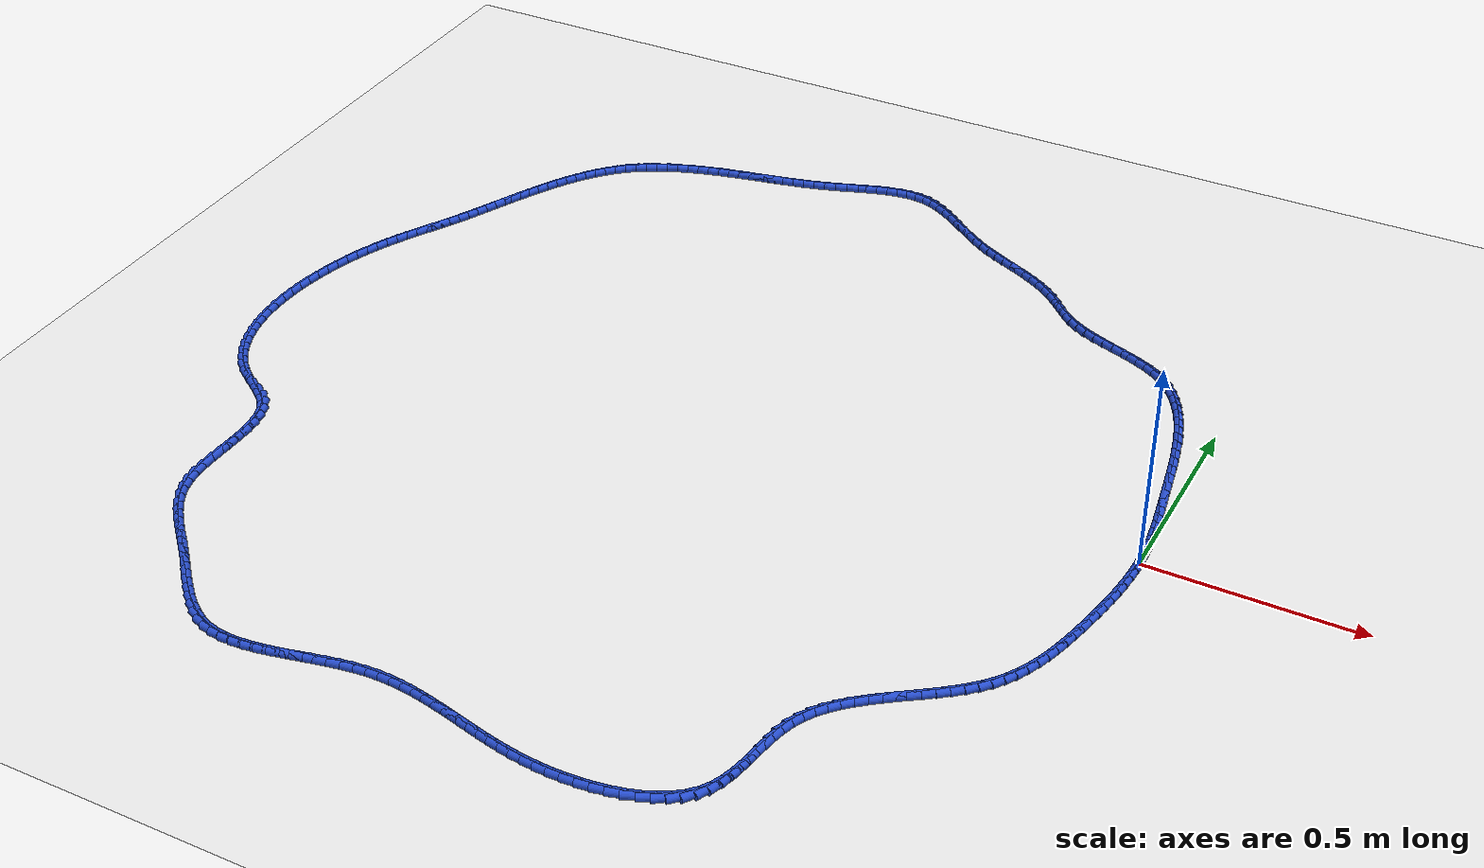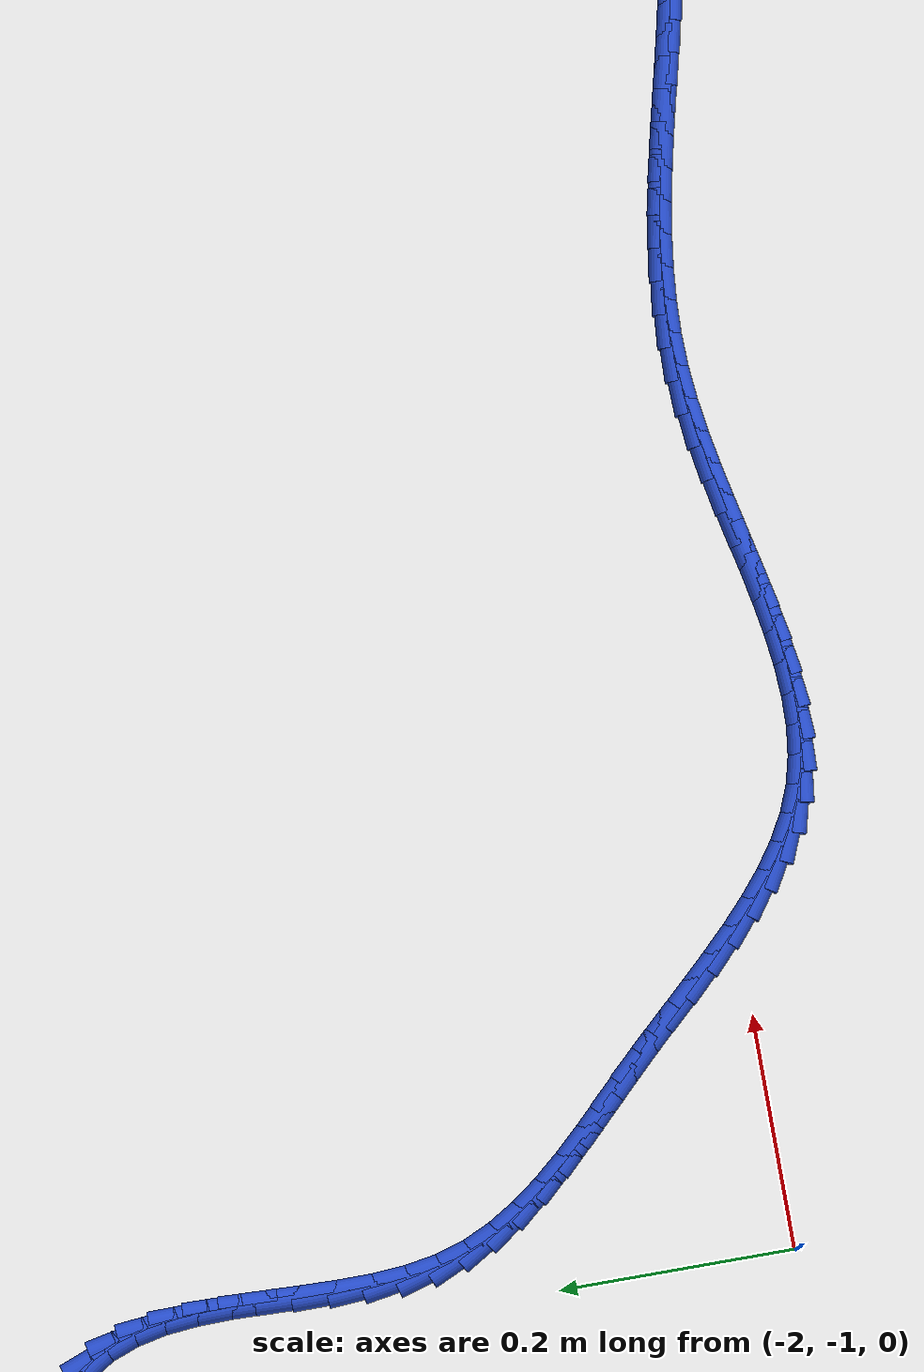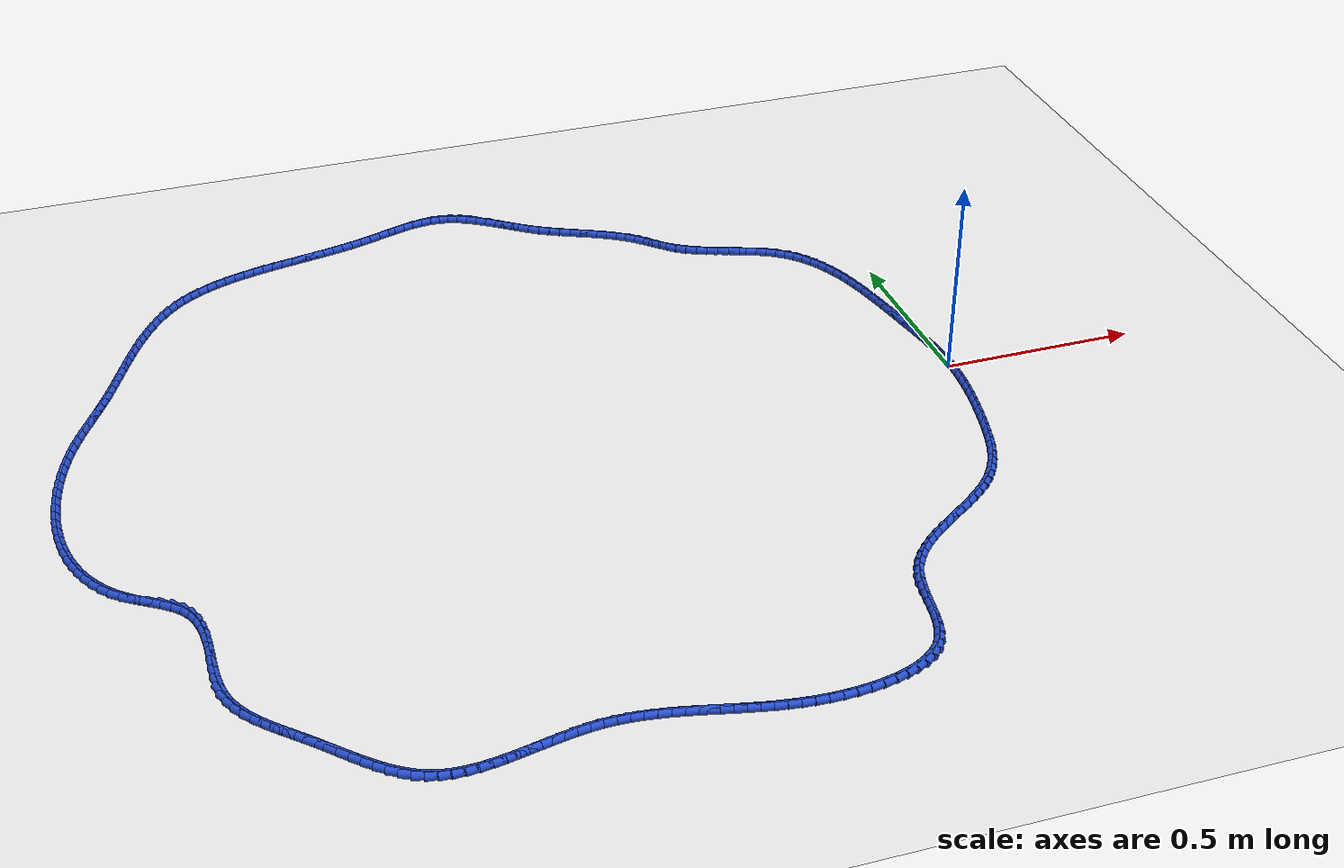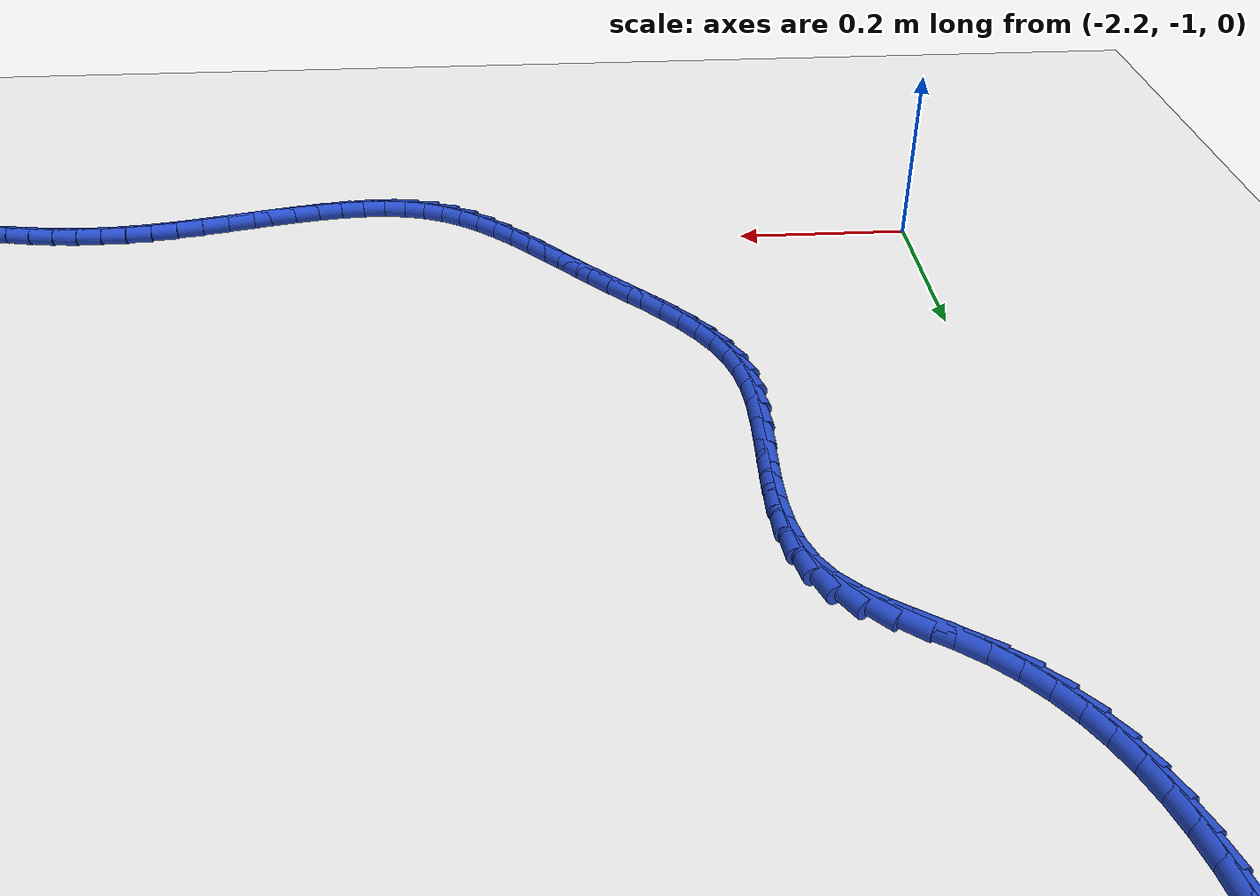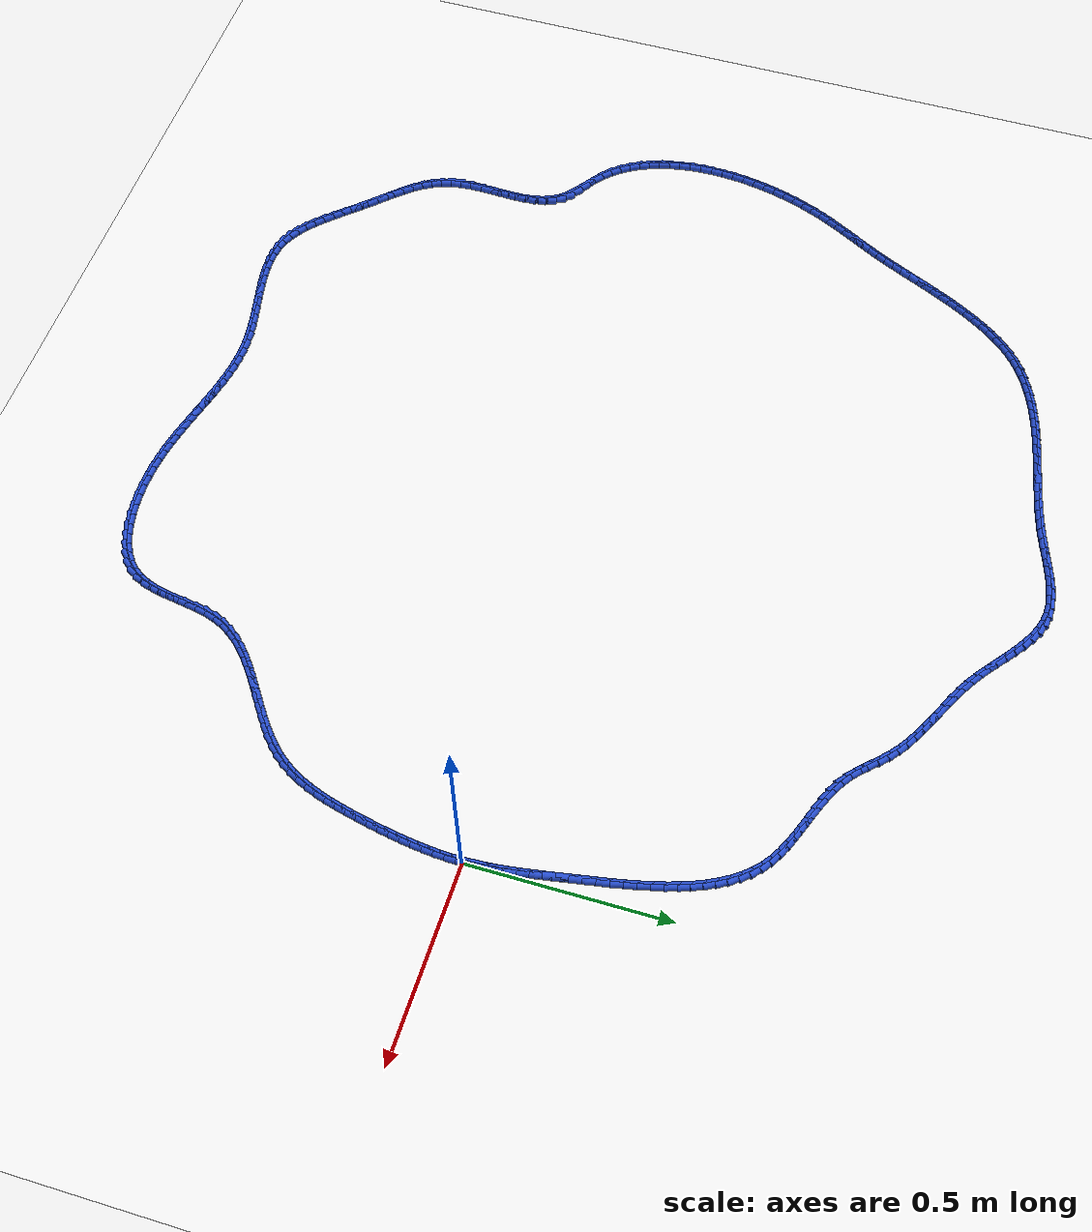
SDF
<sdf version="1.6">
 <world name="default">
  <light name="sun" type="directional">
   <pose>0 0 10 0 -0 0</pose>
   <diffuse>0.8 0.8 0.8 1</diffuse>
   <specular>0.2 0.2 0.2 1</specular>
   <attenuation>
    <range>1000</range>
    <constant>0.9</constant>
    <linear>0.01</linear>
    <quadratic>0.001</quadratic>
   </attenuation>
   <direction>-0.5 0.1 -0.9</direction>
  </light>
  <model name="ground_plane">
   <static>1</static>
   <link name="link">
    <collision name="collision">
     <geometry><plane><normal>0 0 1</normal><size>100 100</size></plane></geometry>
     <surface><friction><ode><mu>100</mu><mu2>50</mu2></ode></friction></surface>
    </collision>
    <visual name="visual">
     <cast_shadows>0</cast_shadows>
     <geometry><plane><normal>0 0 1</normal><size>100 100</size></plane></geometry>
     <material>
      <script><uri>file://media/materials/scripts/gazebo.material</uri><name>Gazebo/WhiteGlow</name></script>
     </material>
    </visual>
   </link>
  </model>
  <gravity>0 0 -9.8</gravity>
  <magnetic_field>6e-06 2.3e-05 -4.2e-05</magnetic_field>
  <atmosphere type="adiabatic"/>
  <physics name="default_physics" default="0" type="ode">
   <max_step_size>0.001</max_step_size>
   <real_time_factor>1</real_time_factor>
   <real_time_update_rate>1000</real_time_update_rate>
  </physics>
  <scene><ambient>0.4 0.4 0.4 1</ambient><background>0.7 0.7 0.7 1</background><shadows>1</shadows></scene>
  <spherical_coordinates>
   <surface_model>EARTH_WGS84</surface_model>
   <latitude_deg>0</latitude_deg>
   <longitude_deg>0</longitude_deg>
   <elevation>0</elevation>
   <heading_deg>0</heading_deg>
  </spherical_coordinates>
  <model name="line">
   <link name="link_0">
    <pose>0.0 -4.163336342344337e-17 0.01 0 1.57 -1.5425747504506282</pose>
    <collision name="collision">
     <geometry><cylinder><radius>0.01</radius><length>0.08</length></cylinder></geometry>
    </collision>
    <visual name="visual">
     <material>
      <script><name>Gazebo/Blue</name><uri>file://media/materials/scripts/gazebo.material</uri></script>
     </material>
     <geometry><cylinder><radius>0.01</radius><length>0.08</length></cylinder></geometry>
    </visual>
   </link>
   <link name="link_1">
    <pose>-0.0007767634482939448 0.027516436651600525 0.01 0 1.57 -1.5067407634336993</pose>
    <collision name="collision">
     <geometry><cylinder><radius>0.01</radius><length>0.08</length></cylinder></geometry>
    </collision>
    <visual name="visual">
     <material>
      <script><name>Gazebo/Blue</name><uri>file://media/materials/scripts/gazebo.material</uri></script>
     </material>
     <geometry><cylinder><radius>0.01</radius><length>0.08</length></cylinder></geometry>
    </visual>
   </link>
   <link name="link_2">
    <pose>-0.0025387742167545307 0.054986340991013224 0.01 0 1.57 -1.475691516393337</pose>
    <collision name="collision">
     <geometry><cylinder><radius>0.01</radius><length>0.08</length></cylinder></geometry>
    </collision>
    <visual name="visual">
     <material>
      <script><name>Gazebo/Blue</name><uri>file://media/materials/scripts/gazebo.material</uri></script>
     </material>
     <geometry><cylinder><radius>0.01</radius><length>0.08</length></cylinder></geometry>
    </visual>
   </link>
   <link name="link_3">
    <pose>-0.005161695182014652 0.08248240707320804 0.01 0 1.57 -1.4496493044596492</pose>
    <collision name="collision">
     <geometry><cylinder><radius>0.01</radius><length>0.08</length></cylinder></geometry>
    </collision>
    <visual name="visual">
     <material>
      <script><name>Gazebo/Blue</name><uri>file://media/materials/scripts/gazebo.material</uri></script>
     </material>
     <geometry><cylinder><radius>0.01</radius><length>0.08</length></cylinder></geometry>
    </visual>
   </link>
   <link name="link_4">
    <pose>-0.008521189220707201 0.11007732895315499 0.01 0 1.57 -1.428719587197607</pose>
    <collision name="collision">
     <geometry><cylinder><radius>0.01</radius><length>0.08</length></cylinder></geometry>
    </collision>
    <visual name="visual">
     <material>
      <script><name>Gazebo/Blue</name><uri>file://media/materials/scripts/gazebo.material</uri></script>
     </material>
     <geometry><cylinder><radius>0.01</radius><length>0.08</length></cylinder></geometry>
    </visual>
   </link>
   <link name="link_5">
    <pose>-0.012492919209465079 0.13784380068582403 0.01 0 1.57 -1.4129099507532425</pose>
    <collision name="collision">
     <geometry><cylinder><radius>0.01</radius><length>0.08</length></cylinder></geometry>
    </collision>
    <visual name="visual">
     <material>
      <script><name>Gazebo/Blue</name><uri>file://media/materials/scripts/gazebo.material</uri></script>
     </material>
     <geometry><cylinder><radius>0.01</radius><length>0.08</length></cylinder></geometry>
    </visual>
   </link>
   <link name="link_6">
    <pose>-0.016952548024921157 0.16585451632618506 0.01 0 1.57 -1.402149222003702</pose>
    <collision name="collision">
     <geometry><cylinder><radius>0.01</radius><length>0.08</length></cylinder></geometry>
    </collision>
    <visual name="visual">
     <material>
      <script><name>Gazebo/Blue</name><uri>file://media/materials/scripts/gazebo.material</uri></script>
     </material>
     <geometry><cylinder><radius>0.01</radius><length>0.08</length></cylinder></geometry>
    </visual>
   </link>
   <link name="link_7">
    <pose>-0.02177573854370835 0.1941821699292082 0.01 0 1.57 -1.396304508381116</pose>
    <collision name="collision">
     <geometry><cylinder><radius>0.01</radius><length>0.08</length></cylinder></geometry>
    </collision>
    <visual name="visual">
     <material>
      <script><name>Gazebo/Blue</name><uri>file://media/materials/scripts/gazebo.material</uri></script>
     </material>
     <geometry><cylinder><radius>0.01</radius><length>0.08</length></cylinder></geometry>
    </visual>
   </link>
   <link name="link_8">
    <pose>-0.02683815364245954 0.22289945554986332 0.01 0 1.57 -1.3951924830440092</pose>
    <collision name="collision">
     <geometry><cylinder><radius>0.01</radius><length>0.08</length></cylinder></geometry>
    </collision>
    <visual name="visual">
     <material>
      <script><name>Gazebo/Blue</name><uri>file://media/materials/scripts/gazebo.material</uri></script>
     </material>
     <geometry><cylinder><radius>0.01</radius><length>0.08</length></cylinder></geometry>
    </visual>
   </link>
   <link name="link_9">
    <pose>-0.032015521711502445 0.2520790029199649 0.01 0 1.57 -1.3963318114265992</pose>
    <collision name="collision">
     <geometry><cylinder><radius>0.01</radius><length>0.08</length></cylinder></geometry>
    </collision>
    <visual name="visual">
     <material>
      <script><name>Gazebo/Blue</name><uri>file://media/materials/scripts/gazebo.material</uri></script>
     </material>
     <geometry><cylinder><radius>0.01</radius><length>0.08</length></cylinder></geometry>
    </visual>
   </link>
   <link name="link_10">
    <pose>-0.0372426578956453 0.28173542876327295 0.01 0 1.57 -1.3932625582505984</pose>
    <collision name="collision">
     <geometry><cylinder><radius>0.01</radius><length>0.08</length></cylinder></geometry>
    </collision>
    <visual name="visual">
     <material>
      <script><name>Gazebo/Blue</name><uri>file://media/materials/scripts/gazebo.material</uri></script>
     </material>
     <geometry><cylinder><radius>0.01</radius><length>0.08</length></cylinder></geometry>
    </visual>
   </link>
   <link name="link_11">
    <pose>-0.042622299834402605 0.311718478858723 0.01 0 1.57 -1.384964978185609</pose>
    <collision name="collision">
     <geometry><cylinder><radius>0.01</radius><length>0.08</length></cylinder></geometry>
    </collision>
    <visual name="visual">
     <material>
      <script><name>Gazebo/Blue</name><uri>file://media/materials/scripts/gazebo.material</uri></script>
     </material>
     <geometry><cylinder><radius>0.01</radius><length>0.08</length></cylinder></geometry>
    </visual>
   </link>
   <link name="link_12">
    <pose>-0.04828681487263271 0.3418488077219059 0.01 0 1.57 -1.3714175723463924</pose>
    <collision name="collision">
     <geometry><cylinder><radius>0.01</radius><length>0.08</length></cylinder></geometry>
    </collision>
    <visual name="visual">
     <material>
      <script><name>Gazebo/Blue</name><uri>file://media/materials/scripts/gazebo.material</uri></script>
     </material>
     <geometry><cylinder><radius>0.01</radius><length>0.08</length></cylinder></geometry>
    </visual>
   </link>
   <link name="link_13">
    <pose>-0.05436857035519397 0.3719470698684126 0.01 0 1.57 -1.3524513216249885</pose>
    <collision name="collision">
     <geometry><cylinder><radius>0.01</radius><length>0.08</length></cylinder></geometry>
    </collision>
    <visual name="visual">
     <material>
      <script><name>Gazebo/Blue</name><uri>file://media/materials/scripts/gazebo.material</uri></script>
     </material>
     <geometry><cylinder><radius>0.01</radius><length>0.08</length></cylinder></geometry>
    </visual>
   </link>
   <link name="link_14">
    <pose>-0.06099993362694474 0.4018339198138341 0.01 0 1.57 -1.3277549563608269</pose>
    <collision name="collision">
     <geometry><cylinder><radius>0.01</radius><length>0.08</length></cylinder></geometry>
    </collision>
    <visual name="visual">
     <material>
      <script><name>Gazebo/Blue</name><uri>file://media/materials/scripts/gazebo.material</uri></script>
     </material>
     <geometry><cylinder><radius>0.01</radius><length>0.08</length></cylinder></geometry>
    </visual>
   </link>
   <link name="link_15">
    <pose>-0.06831327203274337 0.43133001207376115 0.01 0 1.57 -1.2968772920442861</pose>
    <collision name="collision">
     <geometry><cylinder><radius>0.01</radius><length>0.08</length></cylinder></geometry>
    </collision>
    <visual name="visual">
     <material>
      <script><name>Gazebo/Blue</name><uri>file://media/materials/scripts/gazebo.material</uri></script>
     </material>
     <geometry><cylinder><radius>0.01</radius><length>0.08</length></cylinder></geometry>
    </visual>
   </link>
   <link name="link_16">
    <pose>-0.07644095291744828 0.4602560011637852 0.01 0 1.57 -1.259230542531432</pose>
    <collision name="collision">
     <geometry><cylinder><radius>0.01</radius><length>0.08</length></cylinder></geometry>
    </collision>
    <visual name="visual">
     <material>
      <script><name>Gazebo/Blue</name><uri>file://media/materials/scripts/gazebo.material</uri></script>
     </material>
     <geometry><cylinder><radius>0.01</radius><length>0.08</length></cylinder></geometry>
    </visual>
   </link>
   <link name="link_17">
    <pose>-0.08551534362591773 0.48843254159949656 0.01 0 1.57 -1.2141005647863006</pose>
    <collision name="collision">
     <geometry><cylinder><radius>0.01</radius><length>0.08</length></cylinder></geometry>
    </collision>
    <visual name="visual">
     <material>
      <script><name>Gazebo/Blue</name><uri>file://media/materials/scripts/gazebo.material</uri></script>
     </material>
     <geometry><cylinder><radius>0.01</radius><length>0.08</length></cylinder></geometry>
    </visual>
   </link>
   <link name="link_18">
    <pose>-0.09566881150301015 0.5156802878964868 0.01 0 1.57 -1.1606732972444624</pose>
    <collision name="collision">
     <geometry><cylinder><radius>0.01</radius><length>0.08</length></cylinder></geometry>
    </collision>
    <visual name="visual">
     <material>
      <script><name>Gazebo/Blue</name><uri>file://media/materials/scripts/gazebo.material</uri></script>
     </material>
     <geometry><cylinder><radius>0.01</radius><length>0.08</length></cylinder></geometry>
    </visual>
   </link>
   <link name="link_19">
    <pose>-0.10703372389358383 0.5418198945703463 0.01 0 1.57 -1.0980911213470426</pose>
    <collision name="collision">
     <geometry><cylinder><radius>0.01</radius><length>0.08</length></cylinder></geometry>
    </collision>
    <visual name="visual">
     <material>
      <script><name>Gazebo/Blue</name><uri>file://media/materials/scripts/gazebo.material</uri></script>
     </material>
     <geometry><cylinder><radius>0.01</radius><length>0.08</length></cylinder></geometry>
    </visual>
   </link>
   <link name="link_20">
    <pose>-0.11974244814249721 0.5666720161366664 0.01 0 1.57 -1.025557207951859</pose>
    <collision name="collision">
     <geometry><cylinder><radius>0.01</radius><length>0.08</length></cylinder></geometry>
    </collision>
    <visual name="visual">
     <material>
      <script><name>Gazebo/Blue</name><uri>file://media/materials/scripts/gazebo.material</uri></script>
     </material>
     <geometry><cylinder><radius>0.01</radius><length>0.08</length></cylinder></geometry>
    </visual>
   </link>
   <link name="link_21">
    <pose>-0.13392735159460864 0.5900573071110382 0.01 0 1.57 -0.9425061426219088</pose>
    <collision name="collision">
     <geometry><cylinder><radius>0.01</radius><length>0.08</length></cylinder></geometry>
    </collision>
    <visual name="visual">
     <material>
      <script><name>Gazebo/Blue</name><uri>file://media/materials/scripts/gazebo.material</uri></script>
     </material>
     <geometry><cylinder><radius>0.01</radius><length>0.08</length></cylinder></geometry>
    </visual>
   </link>
   <link name="link_22">
    <pose>-0.1497208015947764 0.6117964220090522 0.01 0 1.57 -0.8488471740687971</pose>
    <collision name="collision">
     <geometry><cylinder><radius>0.01</radius><length>0.08</length></cylinder></geometry>
    </collision>
    <visual name="visual">
     <material>
      <script><name>Gazebo/Blue</name><uri>file://media/materials/scripts/gazebo.material</uri></script>
     </material>
     <geometry><cylinder><radius>0.01</radius><length>0.08</length></cylinder></geometry>
    </visual>
   </link>
   <link name="link_23">
    <pose>-0.1672551654878589 0.6317100153462996 0.01 0 1.57 -0.7452518840543317</pose>
    <collision name="collision">
     <geometry><cylinder><radius>0.01</radius><length>0.08</length></cylinder></geometry>
    </collision>
    <visual name="visual">
     <material>
      <script><name>Gazebo/Blue</name><uri>file://media/materials/scripts/gazebo.material</uri></script>
     </material>
     <geometry><cylinder><radius>0.01</radius><length>0.08</length></cylinder></geometry>
    </visual>
   </link>
   <link name="link_24">
    <pose>-0.18666281061871456 0.6496187416383714 0.01 0 1.57 -0.6336413549368419</pose>
    <collision name="collision">
     <geometry><cylinder><radius>0.01</radius><length>0.08</length></cylinder></geometry>
    </collision>
    <visual name="visual">
     <material>
      <script><name>Gazebo/Blue</name><uri>file://media/materials/scripts/gazebo.material</uri></script>
     </material>
     <geometry><cylinder><radius>0.01</radius><length>0.08</length></cylinder></geometry>
    </visual>
   </link>
   <link name="link_25">
    <pose>-0.208072088017075 0.6653482818258402 0.01 0 1.57 -0.528621963700762</pose>
    <collision name="collision">
     <geometry><cylinder><radius>0.01</radius><length>0.08</length></cylinder></geometry>
    </collision>
    <visual name="visual">
     <material>
      <script><name>Gazebo/Blue</name><uri>file://media/materials/scripts/gazebo.material</uri></script>
     </material>
     <geometry><cylinder><radius>0.01</radius><length>0.08</length></cylinder></geometry>
    </visual>
   </link>
   <link name="link_26">
    <pose>-0.23140842551213203 0.678978275568258 0.01 0 1.57 -0.44847335868013116</pose>
    <collision name="collision">
     <geometry><cylinder><radius>0.01</radius><length>0.08</length></cylinder></geometry>
    </collision>
    <visual name="visual">
     <material>
      <script><name>Gazebo/Blue</name><uri>file://media/materials/scripts/gazebo.material</uri></script>
     </material>
     <geometry><cylinder><radius>0.01</radius><length>0.08</length></cylinder></geometry>
    </visual>
   </link>
   <link name="link_27">
    <pose>-0.2563028447152091 0.6909568123906937 0.01 0 1.57 -0.39301074625491556</pose>
    <collision name="collision">
     <geometry><cylinder><radius>0.01</radius><length>0.08</length></cylinder></geometry>
    </collision>
    <visual name="visual">
     <material>
      <script><name>Gazebo/Blue</name><uri>file://media/materials/scripts/gazebo.material</uri></script>
     </material>
     <geometry><cylinder><radius>0.01</radius><length>0.08</length></cylinder></geometry>
    </visual>
   </link>
   <link name="link_28">
    <pose>-0.28236325630949227 0.7017609051827642 0.01 0 1.57 -0.3602006981382695</pose>
    <collision name="collision">
     <geometry><cylinder><radius>0.01</radius><length>0.08</length></cylinder></geometry>
    </collision>
    <visual name="visual">
     <material>
      <script><name>Gazebo/Blue</name><uri>file://media/materials/scripts/gazebo.material</uri></script>
     </material>
     <geometry><cylinder><radius>0.01</radius><length>0.08</length></cylinder></geometry>
    </visual>
   </link>
   <link name="link_29">
    <pose>-0.3091975709781671 0.7118675668340855 0.01 0 1.57 -0.3484292253387665</pose>
    <collision name="collision">
     <geometry><cylinder><radius>0.01</radius><length>0.08</length></cylinder></geometry>
    </collision>
    <visual name="visual">
     <material>
      <script><name>Gazebo/Blue</name><uri>file://media/materials/scripts/gazebo.material</uri></script>
     </material>
     <geometry><cylinder><radius>0.01</radius><length>0.08</length></cylinder></geometry>
    </visual>
   </link>
   <link name="link_30">
    <pose>-0.3364136994044193 0.721753810234274 0.01 0 1.57 -0.356856519039891</pose>
    <collision name="collision">
     <geometry><cylinder><radius>0.01</radius><length>0.08</length></cylinder></geometry>
    </collision>
    <visual name="visual">
     <material>
      <script><name>Gazebo/Blue</name><uri>file://media/materials/scripts/gazebo.material</uri></script>
     </material>
     <geometry><cylinder><radius>0.01</radius><length>0.08</length></cylinder></geometry>
    </visual>
   </link>
   <link name="link_31">
    <pose>-0.36361955227143483 0.7318966482729459 0.01 0 1.57 -0.3854832263349334</pose>
    <collision name="collision">
     <geometry><cylinder><radius>0.01</radius><length>0.08</length></cylinder></geometry>
    </collision>
    <visual name="visual">
     <material>
      <script><name>Gazebo/Blue</name><uri>file://media/materials/scripts/gazebo.material</uri></script>
     </material>
     <geometry><cylinder><radius>0.01</radius><length>0.08</length></cylinder></geometry>
    </visual>
   </link>
   <link name="link_32">
    <pose>-0.3904230402623995 0.7427730938397181 0.01 0 1.57 -0.43503210093595457</pose>
    <collision name="collision">
     <geometry><cylinder><radius>0.01</radius><length>0.08</length></cylinder></geometry>
    </collision>
    <visual name="visual">
     <material>
      <script><name>Gazebo/Blue</name><uri>file://media/materials/scripts/gazebo.material</uri></script>
     </material>
     <geometry><cylinder><radius>0.01</radius><length>0.08</length></cylinder></geometry>
    </visual>
   </link>
   <link name="link_33">
    <pose>-0.4164320740604989 0.7548601598242063 0.01 0 1.57 -0.5066189650234599</pose>
    <collision name="collision">
     <geometry><cylinder><radius>0.01</radius><length>0.08</length></cylinder></geometry>
    </collision>
    <visual name="visual">
     <material>
      <script><name>Gazebo/Blue</name><uri>file://media/materials/scripts/gazebo.material</uri></script>
     </material>
     <geometry><cylinder><radius>0.01</radius><length>0.08</length></cylinder></geometry>
    </visual>
   </link>
   <link name="link_34">
    <pose>-0.44125456434891897 0.7686348591160275 0.01 0 1.57 -0.6010942065488076</pose>
    <collision name="collision">
     <geometry><cylinder><radius>0.01</radius><length>0.08</length></cylinder></geometry>
    </collision>
    <visual name="visual">
     <material>
      <script><name>Gazebo/Blue</name><uri>file://media/materials/scripts/gazebo.material</uri></script>
     </material>
     <geometry><cylinder><radius>0.01</radius><length>0.08</length></cylinder></geometry>
    </visual>
   </link>
   <link name="link_35">
    <pose>-0.4644984225176415 0.7845742036395803 0.01 0 1.57 -0.7054480535789737</pose>
    <collision name="collision">
     <geometry><cylinder><radius>0.01</radius><length>0.08</length></cylinder></geometry>
    </collision>
    <visual name="visual">
     <material>
      <script><name>Gazebo/Blue</name><uri>file://media/materials/scripts/gazebo.material</uri></script>
     </material>
     <geometry><cylinder><radius>0.01</radius><length>0.08</length></cylinder></geometry>
    </visual>
   </link>
   <link name="link_36">
    <pose>-0.48598075872657326 0.8028695188528441 0.01 0 1.57 -0.7707703318666336</pose>
    <collision name="collision">
     <geometry><cylinder><radius>0.01</radius><length>0.08</length></cylinder></geometry>
    </collision>
    <visual name="visual">
     <material>
      <script><name>Gazebo/Blue</name><uri>file://media/materials/scripts/gazebo.material</uri></script>
     </material>
     <geometry><cylinder><radius>0.01</radius><length>0.08</length></cylinder></geometry>
    </visual>
   </link>
   <link name="link_37">
    <pose>-0.5063181062227639 0.8226204203675831 0.01 0 1.57 -0.7865356667090635</pose>
    <collision name="collision">
     <geometry><cylinder><radius>0.01</radius><length>0.08</length></cylinder></geometry>
    </collision>
    <visual name="visual">
     <material>
      <script><name>Gazebo/Blue</name><uri>file://media/materials/scripts/gazebo.material</uri></script>
     </material>
     <geometry><cylinder><radius>0.01</radius><length>0.08</length></cylinder></geometry>
    </visual>
   </link>
   <link name="link_38">
    <pose>-0.5263179247079188 0.8426657904069456 0.01 0 1.57 -0.7528477926509322</pose>
    <collision name="collision">
     <geometry><cylinder><radius>0.01</radius><length>0.08</length></cylinder></geometry>
    </collision>
    <visual name="visual">
     <material>
      <script><name>Gazebo/Blue</name><uri>file://media/materials/scripts/gazebo.material</uri></script>
     </material>
     <geometry><cylinder><radius>0.01</radius><length>0.08</length></cylinder></geometry>
    </visual>
   </link>
   <link name="link_39">
    <pose>-0.5467876738837443 0.8618445111940795 0.01 0 1.57 -0.6765778954506568</pose>
    <collision name="collision">
     <geometry><cylinder><radius>0.01</radius><length>0.08</length></cylinder></geometry>
    </collision>
    <visual name="visual">
     <material>
      <script><name>Gazebo/Blue</name><uri>file://media/materials/scripts/gazebo.material</uri></script>
     </material>
     <geometry><cylinder><radius>0.01</radius><length>0.08</length></cylinder></geometry>
    </visual>
   </link>
   <link name="link_40">
    <pose>-0.56840114780163 0.8792004990527224 0.01 0 1.57 -0.6003460752500569</pose>
    <collision name="collision">
     <geometry><cylinder><radius>0.01</radius><length>0.08</length></cylinder></geometry>
    </collision>
    <visual name="visual">
     <material>
      <script><name>Gazebo/Blue</name><uri>file://media/materials/scripts/gazebo.material</uri></script>
     </material>
     <geometry><cylinder><radius>0.01</radius><length>0.08</length></cylinder></geometry>
    </visual>
   </link>
   <link name="link_41">
    <pose>-0.5911719245562098 0.8947903970959609 0.01 0 1.57 -0.5388591479147657</pose>
    <collision name="collision">
     <geometry><cylinder><radius>0.01</radius><length>0.08</length></cylinder></geometry>
    </collision>
    <visual name="visual">
     <material>
      <script><name>Gazebo/Blue</name><uri>file://media/materials/scripts/gazebo.material</uri></script>
     </material>
     <geometry><cylinder><radius>0.01</radius><length>0.08</length></cylinder></geometry>
    </visual>
   </link>
   <link name="link_42">
    <pose>-0.6149101006261732 0.90898297552423 0.01 0 1.57 -0.49278333056906987</pose>
    <collision name="collision">
     <geometry><cylinder><radius>0.01</radius><length>0.08</length></cylinder></geometry>
    </collision>
    <visual name="visual">
     <material>
      <script><name>Gazebo/Blue</name><uri>file://media/materials/scripts/gazebo.material</uri></script>
     </material>
     <geometry><cylinder><radius>0.01</radius><length>0.08</length></cylinder></geometry>
    </visual>
   </link>
   <link name="link_43">
    <pose>-0.6394257151983435 0.9221470924198305 0.01 0 1.57 -0.4621476209088585</pose>
    <collision name="collision">
     <geometry><cylinder><radius>0.01</radius><length>0.08</length></cylinder></geometry>
    </collision>
    <visual name="visual">
     <material>
      <script><name>Gazebo/Blue</name><uri>file://media/materials/scripts/gazebo.material</uri></script>
     </material>
     <geometry><cylinder><radius>0.01</radius><length>0.08</length></cylinder></geometry>
    </visual>
   </link>
   <link name="link_44">
    <pose>-0.6645288074595429 0.9346516058650617 0.01 0 1.57 -0.44667426147891953</pose>
    <collision name="collision">
     <geometry><cylinder><radius>0.01</radius><length>0.08</length></cylinder></geometry>
    </collision>
    <visual name="visual">
     <material>
      <script><name>Gazebo/Blue</name><uri>file://media/materials/scripts/gazebo.material</uri></script>
     </material>
     <geometry><cylinder><radius>0.01</radius><length>0.08</length></cylinder></geometry>
    </visual>
   </link>
   <link name="link_45">
    <pose>-0.690029416596595 0.9468653739422237 0.01 0 1.57 -0.44600016813956495</pose>
    <collision name="collision">
     <geometry><cylinder><radius>0.01</radius><length>0.08</length></cylinder></geometry>
    </collision>
    <visual name="visual">
     <material>
      <script><name>Gazebo/Blue</name><uri>file://media/materials/scripts/gazebo.material</uri></script>
     </material>
     <geometry><cylinder><radius>0.01</radius><length>0.08</length></cylinder></geometry>
    </visual>
   </link>
   <link name="link_46">
    <pose>-0.7157375817963224 0.9591572547336165 0.01 0 1.57 -0.4597832282691294</pose>
    <collision name="collision">
     <geometry><cylinder><radius>0.01</radius><length>0.08</length></cylinder></geometry>
    </collision>
    <visual name="visual">
     <material>
      <script><name>Gazebo/Blue</name><uri>file://media/materials/scripts/gazebo.material</uri></script>
     </material>
     <geometry><cylinder><radius>0.01</radius><length>0.08</length></cylinder></geometry>
    </visual>
   </link>
   <link name="link_47">
    <pose>-0.7414633422455478 0.9718961063215394 0.01 0 1.57 -0.48770623037120814</pose>
    <collision name="collision">
     <geometry><cylinder><radius>0.01</radius><length>0.08</length></cylinder></geometry>
    </collision>
    <visual name="visual">
     <material>
      <script><name>Gazebo/Blue</name><uri>file://media/materials/scripts/gazebo.material</uri></script>
     </material>
     <geometry><cylinder><radius>0.01</radius><length>0.08</length></cylinder></geometry>
    </visual>
   </link>
   <link name="link_48">
    <pose>-0.7670167371310941 0.9854507867882927 0.01 0 1.57 -0.5293937356290136</pose>
    <collision name="collision">
     <geometry><cylinder><radius>0.01</radius><length>0.08</length></cylinder></geometry>
    </collision>
    <visual name="visual">
     <material>
      <script><name>Gazebo/Blue</name><uri>file://media/materials/scripts/gazebo.material</uri></script>
     </material>
     <geometry><cylinder><radius>0.01</radius><length>0.08</length></cylinder></geometry>
    </visual>
   </link>
   <link name="link_49">
    <pose>-0.7922078056397843 1.000190154216176 0.01 0 1.57 -0.5822283979352211</pose>
    <collision name="collision">
     <geometry><cylinder><radius>0.01</radius><length>0.08</length></cylinder></geometry>
    </collision>
    <visual name="visual">
     <material>
      <script><name>Gazebo/Blue</name><uri>file://media/materials/scripts/gazebo.material</uri></script>
     </material>
     <geometry><cylinder><radius>0.01</radius><length>0.08</length></cylinder></geometry>
    </visual>
   </link>
   <link name="link_50">
    <pose>-0.8168665175469945 1.0164244154298157 0.01 0 1.57 -0.6253963363454006</pose>
    <collision name="collision">
     <geometry><cylinder><radius>0.01</radius><length>0.08</length></cylinder></geometry>
    </collision>
    <visual name="visual">
     <material>
      <script><name>Gazebo/Blue</name><uri>file://media/materials/scripts/gazebo.material</uri></script>
     </material>
     <geometry><cylinder><radius>0.01</radius><length>0.08</length></cylinder></geometry>
    </visual>
   </link>
   <link name="link_51">
    <pose>-0.8410249796978941 1.033868933135995 0.01 0 1.57 -0.6480030467167569</pose>
    <collision name="collision">
     <geometry><cylinder><radius>0.01</radius><length>0.08</length></cylinder></geometry>
    </collision>
    <visual name="visual">
     <material>
      <script><name>Gazebo/Blue</name><uri>file://media/materials/scripts/gazebo.material</uri></script>
     </material>
     <geometry><cylinder><radius>0.01</radius><length>0.08</length></cylinder></geometry>
    </visual>
   </link>
   <link name="link_52">
    <pose>-0.8648329224470125 1.051892930401041 0.01 0 1.57 -0.6505644837466987</pose>
    <collision name="collision">
     <geometry><cylinder><radius>0.01</radius><length>0.08</length></cylinder></geometry>
    </collision>
    <visual name="visual">
     <material>
      <script><name>Gazebo/Blue</name><uri>file://media/materials/scripts/gazebo.material</uri></script>
     </material>
     <geometry><cylinder><radius>0.01</radius><length>0.08</length></cylinder></geometry>
    </visual>
   </link>
   <link name="link_53">
    <pose>-0.8884415345571675 1.069861338522366 0.01 0 1.57 -0.632750825114743</pose>
    <collision name="collision">
     <geometry><cylinder><radius>0.01</radius><length>0.08</length></cylinder></geometry>
    </collision>
    <visual name="visual">
     <material>
      <script><name>Gazebo/Blue</name><uri>file://media/materials/scripts/gazebo.material</uri></script>
     </material>
     <geometry><cylinder><radius>0.01</radius><length>0.08</length></cylinder></geometry>
    </visual>
   </link>
   <link name="link_54">
    <pose>-0.9120020047911771 1.087139088797384 0.01 0 1.57 -0.5931441005881991</pose>
    <collision name="collision">
     <geometry><cylinder><radius>0.01</radius><length>0.08</length></cylinder></geometry>
    </collision>
    <visual name="visual">
     <material>
      <script><name>Gazebo/Blue</name><uri>file://media/materials/scripts/gazebo.material</uri></script>
     </material>
     <geometry><cylinder><radius>0.01</radius><length>0.08</length></cylinder></geometry>
    </visual>
   </link>
   <link name="link_55">
    <pose>-0.9356655219118594 1.103091112523507 0.01 0 1.57 -0.5292966073430971</pose>
    <collision name="collision">
     <geometry><cylinder><radius>0.01</radius><length>0.08</length></cylinder></geometry>
    </collision>
    <visual name="visual">
     <material>
      <script><name>Gazebo/Blue</name><uri>file://media/materials/scripts/gazebo.material</uri></script>
     </material>
     <geometry><cylinder><radius>0.01</radius><length>0.08</length></cylinder></geometry>
    </visual>
   </link>
   <link name="link_56">
    <pose>-0.959583274682032 1.117082340998149 0.01 0 1.57 -0.43813009316804685</pose>
    <collision name="collision">
     <geometry><cylinder><radius>0.01</radius><length>0.08</length></cylinder></geometry>
    </collision>
    <visual name="visual">
     <material>
      <script><name>Gazebo/Blue</name><uri>file://media/materials/scripts/gazebo.material</uri></script>
     </material>
     <geometry><cylinder><radius>0.01</radius><length>0.08</length></cylinder></geometry>
    </visual>
   </link>
   <link name="link_57">
    <pose>-0.9839064518645135 1.1284777055187225 0.01 0 1.57 -0.3170829914901307</pose>
    <collision name="collision">
     <geometry><cylinder><radius>0.01</radius><length>0.08</length></cylinder></geometry>
    </collision>
    <visual name="visual">
     <material>
      <script><name>Gazebo/Blue</name><uri>file://media/materials/scripts/gazebo.material</uri></script>
     </material>
     <geometry><cylinder><radius>0.01</radius><length>0.08</length></cylinder></geometry>
    </visual>
   </link>
   <link name="link_58">
    <pose>-1.0087862422221214 1.1366421373826407 0.01 0 1.57 -0.16775414747583386</pose>
    <collision name="collision">
     <geometry><cylinder><radius>0.01</radius><length>0.08</length></cylinder></geometry>
    </collision>
    <visual name="visual">
     <material>
      <script><name>Gazebo/Blue</name><uri>file://media/materials/scripts/gazebo.material</uri></script>
     </material>
     <geometry><cylinder><radius>0.01</radius><length>0.08</length></cylinder></geometry>
    </visual>
   </link>
   <link name="link_59">
    <pose>-1.0343667691493539 1.1409740891177365 0.01 0 1.57 -0.019884113593531202</pose>
    <collision name="collision">
     <geometry><cylinder><radius>0.01</radius><length>0.08</length></cylinder></geometry>
    </collision>
    <visual name="visual">
     <material>
      <script><name>Gazebo/Blue</name><uri>file://media/materials/scripts/gazebo.material</uri></script>
     </material>
     <geometry><cylinder><radius>0.01</radius><length>0.08</length></cylinder></geometry>
    </visual>
   </link>
   <link name="link_60">
    <pose>-1.060660429085584 1.1414969841542413 0.01 0 1.57 0.10037707467782653</pose>
    <collision name="collision">
     <geometry><cylinder><radius>0.01</radius><length>0.08</length></cylinder></geometry>
    </collision>
    <visual name="visual">
     <material>
      <script><name>Gazebo/Blue</name><uri>file://media/materials/scripts/gazebo.material</uri></script>
     </material>
     <geometry><cylinder><radius>0.01</radius><length>0.08</length></cylinder></geometry>
    </visual>
   </link>
   <link name="link_61">
    <pose>-1.0875630126536087 1.1387874754595328 0.01 0 1.57 0.19267171252004192</pose>
    <collision name="collision">
     <geometry><cylinder><radius>0.01</radius><length>0.08</length></cylinder></geometry>
    </collision>
    <visual name="visual">
     <material>
      <script><name>Gazebo/Blue</name><uri>file://media/materials/scripts/gazebo.material</uri></script>
     </material>
     <geometry><cylinder><radius>0.01</radius><length>0.08</length></cylinder></geometry>
    </visual>
   </link>
   <link name="link_62">
    <pose>-1.1149662834373986 1.1334413220532453 0.01 0 1.57 0.2597573451441378</pose>
    <collision name="collision">
     <geometry><cylinder><radius>0.01</radius><length>0.08</length></cylinder></geometry>
    </collision>
    <visual name="visual">
     <material>
      <script><name>Gazebo/Blue</name><uri>file://media/materials/scripts/gazebo.material</uri></script>
     </material>
     <geometry><cylinder><radius>0.01</radius><length>0.08</length></cylinder></geometry>
    </visual>
   </link>
   <link name="link_63">
    <pose>-1.1427620050209246 1.1260542829550129 0.01 0 1.57 0.3047391400324592</pose>
    <collision name="collision">
     <geometry><cylinder><radius>0.01</radius><length>0.08</length></cylinder></geometry>
    </collision>
    <visual name="visual">
     <material>
      <script><name>Gazebo/Blue</name><uri>file://media/materials/scripts/gazebo.material</uri></script>
     </material>
     <geometry><cylinder><radius>0.01</radius><length>0.08</length></cylinder></geometry>
    </visual>
   </link>
   <link name="link_64">
    <pose>-1.1708419409881587 1.117222117184471 0.01 0 1.57 0.33010072968656384</pose>
    <collision name="collision">
     <geometry><cylinder><radius>0.01</radius><length>0.08</length></cylinder></geometry>
    </collision>
    <visual name="visual">
     <material>
      <script><name>Gazebo/Blue</name><uri>file://media/materials/scripts/gazebo.material</uri></script>
     </material>
     <geometry><cylinder><radius>0.01</radius><length>0.08</length></cylinder></geometry>
    </visual>
   </link>
   <link name="link_65">
    <pose>-1.199097854923071 1.1075405837612529 0.01 0 1.57 0.3373623029033773</pose>
    <collision name="collision">
     <geometry><cylinder><radius>0.01</radius><length>0.08</length></cylinder></geometry>
    </collision>
    <visual name="visual">
     <material>
      <script><name>Gazebo/Blue</name><uri>file://media/materials/scripts/gazebo.material</uri></script>
     </material>
     <geometry><cylinder><radius>0.01</radius><length>0.08</length></cylinder></geometry>
    </visual>
   </link>
   <link name="link_66">
    <pose>-1.2274215104096335 1.0976054417049936 0.01 0 1.57 0.3270004151127906</pose>
    <collision name="collision">
     <geometry><cylinder><radius>0.01</radius><length>0.08</length></cylinder></geometry>
    </collision>
    <visual name="visual">
     <material>
      <script><name>Gazebo/Blue</name><uri>file://media/materials/scripts/gazebo.material</uri></script>
     </material>
     <geometry><cylinder><radius>0.01</radius><length>0.08</length></cylinder></geometry>
    </visual>
   </link>
   <link name="link_67">
    <pose>-1.2557046710318165 1.0880124500353276 0.01 0 1.57 0.3005778866389889</pose>
    <collision name="collision">
     <geometry><cylinder><radius>0.01</radius><length>0.08</length></cylinder></geometry>
    </collision>
    <visual name="visual">
     <material>
      <script><name>Gazebo/Blue</name><uri>file://media/materials/scripts/gazebo.material</uri></script>
     </material>
     <geometry><cylinder><radius>0.01</radius><length>0.08</length></cylinder></geometry>
    </visual>
   </link>
   <link name="link_68">
    <pose>-1.2838501892593501 1.0792881965038106 0.01 0 1.57 0.27201113206563127</pose>
    <collision name="collision">
     <geometry><cylinder><radius>0.01</radius><length>0.08</length></cylinder></geometry>
    </collision>
    <visual name="visual">
     <material>
      <script><name>Gazebo/Blue</name><uri>file://media/materials/scripts/gazebo.material</uri></script>
     </material>
     <geometry><cylinder><radius>0.01</radius><length>0.08</length></cylinder></geometry>
    </visual>
   </link>
   <link name="link_69">
    <pose>-1.3118374507641708 1.071481863037655 0.01 0 1.57 0.24769769130573802</pose>
    <collision name="collision">
     <geometry><cylinder><radius>0.01</radius><length>0.08</length></cylinder></geometry>
    </collision>
    <visual name="visual">
     <material>
      <script><name>Gazebo/Blue</name><uri>file://media/materials/scripts/gazebo.material</uri></script>
     </material>
     <geometry><cylinder><radius>0.01</radius><length>0.08</length></cylinder></geometry>
    </visual>
   </link>
   <link name="link_70">
    <pose>-1.339678131693805 1.0644412070754432 0.01 0 1.57 0.2279727099803743</pose>
    <collision name="collision">
     <geometry><cylinder><radius>0.01</radius><length>0.08</length></cylinder></geometry>
    </collision>
    <visual name="visual">
     <material>
      <script><name>Gazebo/Blue</name><uri>file://media/materials/scripts/gazebo.material</uri></script>
     </material>
     <geometry><cylinder><radius>0.01</radius><length>0.08</length></cylinder></geometry>
    </visual>
   </link>
   <link name="link_71">
    <pose>-1.3673840220418303 1.0580132758964162 0.01 0 1.57 0.21308696646675304</pose>
    <collision name="collision">
     <geometry><cylinder><radius>0.01</radius><length>0.08</length></cylinder></geometry>
    </collision>
    <visual name="visual">
     <material>
      <script><name>Gazebo/Blue</name><uri>file://media/materials/scripts/gazebo.material</uri></script>
     </material>
     <geometry><cylinder><radius>0.01</radius><length>0.08</length></cylinder></geometry>
    </visual>
   </link>
   <link name="link_72">
    <pose>-1.3949669118018269 1.0520451167798177 0.01 0 1.57 0.20323398639800752</pose>
    <collision name="collision">
     <geometry><cylinder><radius>0.01</radius><length>0.08</length></cylinder></geometry>
    </collision>
    <visual name="visual">
     <material>
      <script><name>Gazebo/Blue</name><uri>file://media/materials/scripts/gazebo.material</uri></script>
     </material>
     <geometry><cylinder><radius>0.01</radius><length>0.08</length></cylinder></geometry>
    </visual>
   </link>
   <link name="link_73">
    <pose>-1.4224385909673714 1.0463837770048878 0.01 0 1.57 0.19855527441415055</pose>
    <collision name="collision">
     <geometry><cylinder><radius>0.01</radius><length>0.08</length></cylinder></geometry>
    </collision>
    <visual name="visual">
     <material>
      <script><name>Gazebo/Blue</name><uri>file://media/materials/scripts/gazebo.material</uri></script>
     </material>
     <geometry><cylinder><radius>0.01</radius><length>0.08</length></cylinder></geometry>
    </visual>
   </link>
   <link name="link_74">
    <pose>-1.4498108495320434 1.0408763038508693 0.01 0 1.57 0.19914408789378646</pose>
    <collision name="collision">
     <geometry><cylinder><radius>0.01</radius><length>0.08</length></cylinder></geometry>
    </collision>
    <visual name="visual">
     <material>
      <script><name>Gazebo/Blue</name><uri>file://media/materials/scripts/gazebo.material</uri></script>
     </material>
     <geometry><cylinder><radius>0.01</radius><length>0.08</length></cylinder></geometry>
    </visual>
   </link>
   <link name="link_75">
    <pose>-1.4770954774894223 1.0353697445970038 0.01 0 1.57 0.20504667120053235</pose>
    <collision name="collision">
     <geometry><cylinder><radius>0.01</radius><length>0.08</length></cylinder></geometry>
    </collision>
    <visual name="visual">
     <material>
      <script><name>Gazebo/Blue</name><uri>file://media/materials/scripts/gazebo.material</uri></script>
     </material>
     <geometry><cylinder><radius>0.01</radius><length>0.08</length></cylinder></geometry>
    </visual>
   </link>
   <link name="link_76">
    <pose>-1.504304264833086 1.0297111465225335 0.01 0 1.57 0.21626030453882042</pose>
    <collision name="collision">
     <geometry><cylinder><radius>0.01</radius><length>0.08</length></cylinder></geometry>
    </collision>
    <visual name="visual">
     <material>
      <script><name>Gazebo/Blue</name><uri>file://media/materials/scripts/gazebo.material</uri></script>
     </material>
     <geometry><cylinder><radius>0.01</radius><length>0.08</length></cylinder></geometry>
    </visual>
   </link>
   <link name="link_77">
    <pose>-1.5314490015566122 1.0237475569066996 0.01 0 1.57 0.2327280087937068</pose>
    <collision name="collision">
     <geometry><cylinder><radius>0.01</radius><length>0.08</length></cylinder></geometry>
    </collision>
    <visual name="visual">
     <material>
      <script><name>Gazebo/Blue</name><uri>file://media/materials/scripts/gazebo.material</uri></script>
     </material>
     <geometry><cylinder><radius>0.01</radius><length>0.08</length></cylinder></geometry>
    </visual>
   </link>
   <link name="link_78">
    <pose>-1.5585414776535809 1.0173260230287444 0.01 0 1.57 0.2543302973593069</pose>
    <collision name="collision">
     <geometry><cylinder><radius>0.01</radius><length>0.08</length></cylinder></geometry>
    </collision>
    <visual name="visual">
     <material>
      <script><name>Gazebo/Blue</name><uri>file://media/materials/scripts/gazebo.material</uri></script>
     </material>
     <geometry><cylinder><radius>0.01</radius><length>0.08</length></cylinder></geometry>
    </visual>
   </link>
   <link name="link_79">
    <pose>-1.5855934831175695 1.0102935921679095 0.01 0 1.57 0.28087498554764667</pose>
    <collision name="collision">
     <geometry><cylinder><radius>0.01</radius><length>0.08</length></cylinder></geometry>
    </collision>
    <visual name="visual">
     <material>
      <script><name>Gazebo/Blue</name><uri>file://media/materials/scripts/gazebo.material</uri></script>
     </material>
     <geometry><cylinder><radius>0.01</radius><length>0.08</length></cylinder></geometry>
    </visual>
   </link>
   <link name="link_80">
    <pose>-1.6126168079421572 1.0024973116034372 0.01 0 1.57 0.3122426797753947</pose>
    <collision name="collision">
     <geometry><cylinder><radius>0.01</radius><length>0.08</length></cylinder></geometry>
    </collision>
    <visual name="visual">
     <material>
      <script><name>Gazebo/Blue</name><uri>file://media/materials/scripts/gazebo.material</uri></script>
     </material>
     <geometry><cylinder><radius>0.01</radius><length>0.08</length></cylinder></geometry>
    </visual>
   </link>
   <link name="link_81">
    <pose>-1.639595160303173 0.9937886431454803 0.01 0 1.57 0.34915072345688863</pose>
    <collision name="collision">
     <geometry><cylinder><radius>0.01</radius><length>0.08</length></cylinder></geometry>
    </collision>
    <visual name="visual">
     <material>
      <script><name>Gazebo/Blue</name><uri>file://media/materials/scripts/gazebo.material</uri></script>
     </material>
     <geometry><cylinder><radius>0.01</radius><length>0.08</length></cylinder></geometry>
    </visual>
   </link>
   <link name="link_82">
    <pose>-1.6663671695606455 0.9840418553513376 0.01 0 1.57 0.3922335474188446</pose>
    <collision name="collision">
     <geometry><cylinder><radius>0.01</radius><length>0.08</length></cylinder></geometry>
    </collision>
    <visual name="visual">
     <material>
      <script><name>Gazebo/Blue</name><uri>file://media/materials/scripts/gazebo.material</uri></script>
     </material>
     <geometry><cylinder><radius>0.01</radius><length>0.08</length></cylinder></geometry>
    </visual>
   </link>
   <link name="link_83">
    <pose>-1.6927247515836117 0.97313856025414 0.01 0 1.57 0.4419901675397512</pose>
    <collision name="collision">
     <geometry><cylinder><radius>0.01</radius><length>0.08</length></cylinder></geometry>
    </collision>
    <visual name="visual">
     <material>
      <script><name>Gazebo/Blue</name><uri>file://media/materials/scripts/gazebo.material</uri></script>
     </material>
     <geometry><cylinder><radius>0.01</radius><length>0.08</length></cylinder></geometry>
    </visual>
   </link>
   <link name="link_84">
    <pose>-1.7184597997865754 0.9609603734169256 0.01 0 1.57 0.4989517790778436</pose>
    <collision name="collision">
     <geometry><cylinder><radius>0.01</radius><length>0.08</length></cylinder></geometry>
    </collision>
    <visual name="visual">
     <material>
      <script><name>Gazebo/Blue</name><uri>file://media/materials/scripts/gazebo.material</uri></script>
     </material>
     <geometry><cylinder><radius>0.01</radius><length>0.08</length></cylinder></geometry>
    </visual>
   </link>
   <link name="link_85">
    <pose>-1.743364207584042 0.9473889104027328 0.01 0 1.57 0.563617972813412</pose>
    <collision name="collision">
     <geometry><cylinder><radius>0.01</radius><length>0.08</length></cylinder></geometry>
    </collision>
    <visual name="visual">
     <material>
      <script><name>Gazebo/Blue</name><uri>file://media/materials/scripts/gazebo.material</uri></script>
     </material>
     <geometry><cylinder><radius>0.01</radius><length>0.08</length></cylinder></geometry>
    </visual>
   </link>
   <link name="link_86">
    <pose>-1.7672298683905145 0.9323057867745993 0.01 0 1.57 0.6363607128908866</pose>
    <collision name="collision">
     <geometry><cylinder><radius>0.01</radius><length>0.08</length></cylinder></geometry>
    </collision>
    <visual name="visual">
     <material>
      <script><name>Gazebo/Blue</name><uri>file://media/materials/scripts/gazebo.material</uri></script>
     </material>
     <geometry><cylinder><radius>0.01</radius><length>0.08</length></cylinder></geometry>
    </visual>
   </link>
   <link name="link_87">
    <pose>-1.7898487197560158 0.9155926638061955 0.01 0 1.57 0.7138617305378235</pose>
    <collision name="collision">
     <geometry><cylinder><radius>0.01</radius><length>0.08</length></cylinder></geometry>
    </collision>
    <visual name="visual">
     <material>
      <script><name>Gazebo/Blue</name><uri>file://media/materials/scripts/gazebo.material</uri></script>
     </material>
     <geometry><cylinder><radius>0.01</radius><length>0.08</length></cylinder></geometry>
    </visual>
   </link>
   <link name="link_88">
    <pose>-1.8110799087837208 0.8972008109076568 0.01 0 1.57 0.7855044198799838</pose>
    <collision name="collision">
     <geometry><cylinder><radius>0.01</radius><length>0.08</length></cylinder></geometry>
    </collision>
    <visual name="visual">
     <material>
      <script><name>Gazebo/Blue</name><uri>file://media/materials/scripts/gazebo.material</uri></script>
     </material>
     <geometry><cylinder><radius>0.01</radius><length>0.08</length></cylinder></geometry>
    </visual>
   </link>
   <link name="link_89">
    <pose>-1.8309851720811545 0.8772913170341572 0.01 0 1.57 0.8491514623641381</pose>
    <collision name="collision">
     <geometry><cylinder><radius>0.01</radius><length>0.08</length></cylinder></geometry>
    </collision>
    <visual name="visual">
     <material>
      <script><name>Gazebo/Blue</name><uri>file://media/materials/scripts/gazebo.material</uri></script>
     </material>
     <geometry><cylinder><radius>0.01</radius><length>0.08</length></cylinder></geometry>
    </visual>
   </link>
   <link name="link_90">
    <pose>-1.8496642654399171 0.8560646471585555 0.01 0 1.57 0.904905527890935</pose>
    <collision name="collision">
     <geometry><cylinder><radius>0.01</radius><length>0.08</length></cylinder></geometry>
    </collision>
    <visual name="visual">
     <material>
      <script><name>Gazebo/Blue</name><uri>file://media/materials/scripts/gazebo.material</uri></script>
     </material>
     <geometry><cylinder><radius>0.01</radius><length>0.08</length></cylinder></geometry>
    </visual>
   </link>
   <link name="link_91">
    <pose>-1.8672169446516105 0.8337212662537108 0.01 0 1.57 0.9530564917022778</pose>
    <collision name="collision">
     <geometry><cylinder><radius>0.01</radius><length>0.08</length></cylinder></geometry>
    </collision>
    <visual name="visual">
     <material>
      <script><name>Gazebo/Blue</name><uri>file://media/materials/scripts/gazebo.material</uri></script>
     </material>
     <geometry><cylinder><radius>0.01</radius><length>0.08</length></cylinder></geometry>
    </visual>
   </link>
   <link name="link_92">
    <pose>-1.8837429655078357 0.8104616392924819 0.01 0 1.57 0.9939783937500359</pose>
    <collision name="collision">
     <geometry><cylinder><radius>0.01</radius><length>0.08</length></cylinder></geometry>
    </collision>
    <visual name="visual">
     <material>
      <script><name>Gazebo/Blue</name><uri>file://media/materials/scripts/gazebo.material</uri></script>
     </material>
     <geometry><cylinder><radius>0.01</radius><length>0.08</length></cylinder></geometry>
    </visual>
   </link>
   <link name="link_93">
    <pose>-1.8993420838001935 0.7864862312477275 0.01 0 1.57 1.0280541290480876</pose>
    <collision name="collision">
     <geometry><cylinder><radius>0.01</radius><length>0.08</length></cylinder></geometry>
    </collision>
    <visual name="visual">
     <material>
      <script><name>Gazebo/Blue</name><uri>file://media/materials/scripts/gazebo.material</uri></script>
     </material>
     <geometry><cylinder><radius>0.01</radius><length>0.08</length></cylinder></geometry>
    </visual>
   </link>
   <link name="link_94">
    <pose>-1.9141140614398982 0.7619953876167522 0.01 0 1.57 1.0561872339718896</pose>
    <collision name="collision">
     <geometry><cylinder><radius>0.01</radius><length>0.08</length></cylinder></geometry>
    </collision>
    <visual name="visual">
     <material>
      <script><name>Gazebo/Blue</name><uri>file://media/materials/scripts/gazebo.material</uri></script>
     </material>
     <geometry><cylinder><radius>0.01</radius><length>0.08</length></cylinder></geometry>
    </visual>
   </link>
   <link name="link_95">
    <pose>-1.9281605219783573 0.7371531083733968 0.01 0 1.57 1.0798696321446573</pose>
    <collision name="collision">
     <geometry><cylinder><radius>0.01</radius><length>0.08</length></cylinder></geometry>
    </collision>
    <visual name="visual">
     <material>
      <script><name>Gazebo/Blue</name><uri>file://media/materials/scripts/gazebo.material</uri></script>
     </material>
     <geometry><cylinder><radius>0.01</radius><length>0.08</length></cylinder></geometry>
    </visual>
   </link>
   <link name="link_96">
    <pose>-1.9415875613641878 0.7120360771465155 0.01 0 1.57 1.099270968803575</pose>
    <collision name="collision">
     <geometry><cylinder><radius>0.01</radius><length>0.08</length></cylinder></geometry>
    </collision>
    <visual name="visual">
     <material>
      <script><name>Gazebo/Blue</name><uri>file://media/materials/scripts/gazebo.material</uri></script>
     </material>
     <geometry><cylinder><radius>0.01</radius><length>0.08</length></cylinder></geometry>
    </visual>
   </link>
   <link name="link_97">
    <pose>-1.9545019334030098 0.6867081339675486 0.01 0 1.57 1.114367454907676</pose>
    <collision name="collision">
     <geometry><cylinder><radius>0.01</radius><length>0.08</length></cylinder></geometry>
    </collision>
    <visual name="visual">
     <material>
      <script><name>Gazebo/Blue</name><uri>file://media/materials/scripts/gazebo.material</uri></script>
     </material>
     <geometry><cylinder><radius>0.01</radius><length>0.08</length></cylinder></geometry>
    </visual>
   </link>
   <link name="link_98">
    <pose>-1.9670103919004442 0.6612331188679361 0.01 0 1.57 1.1251433832271764</pose>
    <collision name="collision">
     <geometry><cylinder><radius>0.01</radius><length>0.08</length></cylinder></geometry>
    </collision>
    <visual name="visual">
     <material>
      <script><name>Gazebo/Blue</name><uri>file://media/materials/scripts/gazebo.material</uri></script>
     </material>
     <geometry><cylinder><radius>0.01</radius><length>0.08</length></cylinder></geometry>
    </visual>
   </link>
   <link name="link_99">
    <pose>-1.9792196906621116 0.6356748718791186 0.01 0 1.57 1.1315826722138764</pose>
    <collision name="collision">
     <geometry><cylinder><radius>0.01</radius><length>0.08</length></cylinder></geometry>
    </collision>
    <visual name="visual">
     <material>
      <script><name>Gazebo/Blue</name><uri>file://media/materials/scripts/gazebo.material</uri></script>
     </material>
     <geometry><cylinder><radius>0.01</radius><length>0.08</length></cylinder></geometry>
    </visual>
   </link>
   <link name="link_100">
    <pose>-1.9912365834936323 0.6100972330325362 0.01 0 1.57 1.1336626986108702</pose>
    <collision name="collision">
     <geometry><cylinder><radius>0.01</radius><length>0.08</length></cylinder></geometry>
    </collision>
    <visual name="visual">
     <material>
      <script><name>Gazebo/Blue</name><uri>file://media/materials/scripts/gazebo.material</uri></script>
     </material>
     <geometry><cylinder><radius>0.01</radius><length>0.08</length></cylinder></geometry>
    </visual>
   </link>
   <link name="link_101">
    <pose>-2.0031678242006272 0.5845640423596291 0.01 0 1.57 1.1313504518986628</pose>
    <collision name="collision">
     <geometry><cylinder><radius>0.01</radius><length>0.08</length></cylinder></geometry>
    </collision>
    <visual name="visual">
     <material>
      <script><name>Gazebo/Blue</name><uri>file://media/materials/scripts/gazebo.material</uri></script>
     </material>
     <geometry><cylinder><radius>0.01</radius><length>0.08</length></cylinder></geometry>
    </visual>
   </link>
   <link name="link_102">
    <pose>-2.015120166588718 0.5591391398918379 0.01 0 1.57 1.1246010553671206</pose>
    <collision name="collision">
     <geometry><cylinder><radius>0.01</radius><length>0.08</length></cylinder></geometry>
    </collision>
    <visual name="visual">
     <material>
      <script><name>Gazebo/Blue</name><uri>file://media/materials/scripts/gazebo.material</uri></script>
     </material>
     <geometry><cylinder><radius>0.01</radius><length>0.08</length></cylinder></geometry>
    </visual>
   </link>
   <link name="link_103">
    <pose>-2.0272003644635235 0.5338863656606025 0.01 0 1.57 1.1133587654145527</pose>
    <collision name="collision">
     <geometry><cylinder><radius>0.01</radius><length>0.08</length></cylinder></geometry>
    </collision>
    <visual name="visual">
     <material>
      <script><name>Gazebo/Blue</name><uri>file://media/materials/scripts/gazebo.material</uri></script>
     </material>
     <geometry><cylinder><radius>0.01</radius><length>0.08</length></cylinder></geometry>
    </visual>
   </link>
   <link name="link_104">
    <pose>-2.0395151716306663 0.5088695596973636 0.01 0 1.57 1.0975617156202602</pose>
    <collision name="collision">
     <geometry><cylinder><radius>0.01</radius><length>0.08</length></cylinder></geometry>
    </collision>
    <visual name="visual">
     <material>
      <script><name>Gazebo/Blue</name><uri>file://media/materials/scripts/gazebo.material</uri></script>
     </material>
     <geometry><cylinder><radius>0.01</radius><length>0.08</length></cylinder></geometry>
    </visual>
   </link>
   <link name="link_105">
    <pose>-2.0521713195485476 0.48415254084369885 0.01 0 1.57 1.0797283366177564</pose>
    <collision name="collision">
     <geometry><cylinder><radius>0.01</radius><length>0.08</length></cylinder></geometry>
    </collision>
    <visual name="visual">
     <material>
      <script><name>Gazebo/Blue</name><uri>file://media/materials/scripts/gazebo.material</uri></script>
     </material>
     <geometry><cylinder><radius>0.01</radius><length>0.08</length></cylinder></geometry>
    </visual>
   </link>
   <link name="link_106">
    <pose>-2.0652218124888133 0.4597481832683741 0.01 0 1.57 1.0680367067449057</pose>
    <collision name="collision">
     <geometry><cylinder><radius>0.01</radius><length>0.08</length></cylinder></geometry>
    </collision>
    <visual name="visual">
     <material>
      <script><name>Gazebo/Blue</name><uri>file://media/materials/scripts/gazebo.material</uri></script>
     </material>
     <geometry><cylinder><radius>0.01</radius><length>0.08</length></cylinder></geometry>
    </visual>
   </link>
   <link name="link_107">
    <pose>-2.078550659407238 0.43550911803804604 0.01 0 1.57 1.064188887965418</pose>
    <collision name="collision">
     <geometry><cylinder><radius>0.01</radius><length>0.08</length></cylinder></geometry>
    </collision>
    <visual name="visual">
     <material>
      <script><name>Gazebo/Blue</name><uri>file://media/materials/scripts/gazebo.material</uri></script>
     </material>
     <geometry><cylinder><radius>0.01</radius><length>0.08</length></cylinder></geometry>
    </visual>
   </link>
   <link name="link_108">
    <pose>-2.092008726966153 0.4112565503547838 0.01 0 1.57 1.0681579431897192</pose>
    <collision name="collision">
     <geometry><cylinder><radius>0.01</radius><length>0.08</length></cylinder></geometry>
    </collision>
    <visual name="visual">
     <material>
      <script><name>Gazebo/Blue</name><uri>file://media/materials/scripts/gazebo.material</uri></script>
     </material>
     <geometry><cylinder><radius>0.01</radius><length>0.08</length></cylinder></geometry>
    </visual>
   </link>
   <link name="link_109">
    <pose>-2.105446881827889 0.3868116854206559 0.01 0 1.57 1.0797750694802153</pose>
    <collision name="collision">
     <geometry><cylinder><radius>0.01</radius><length>0.08</length></cylinder></geometry>
    </collision>
    <visual name="visual">
     <material>
      <script><name>Gazebo/Blue</name><uri>file://media/materials/scripts/gazebo.material</uri></script>
     </material>
     <geometry><cylinder><radius>0.01</radius><length>0.08</length></cylinder></geometry>
    </visual>
   </link>
   <link name="link_110">
    <pose>-2.1187159906547772 0.36199572843773103 0.01 0 1.57 1.0987319402519897</pose>
    <collision name="collision">
     <geometry><cylinder><radius>0.01</radius><length>0.08</length></cylinder></geometry>
    </collision>
    <visual name="visual">
     <material>
      <script><name>Gazebo/Blue</name><uri>file://media/materials/scripts/gazebo.material</uri></script>
     </material>
     <geometry><cylinder><radius>0.01</radius><length>0.08</length></cylinder></geometry>
    </visual>
   </link>
   <link name="link_111">
    <pose>-2.131666920109149 0.33662988460807786 0.01 0 1.57 1.124577685523759</pose>
    <collision name="collision">
     <geometry><cylinder><radius>0.01</radius><length>0.08</length></cylinder></geometry>
    </collision>
    <visual name="visual">
     <material>
      <script><name>Gazebo/Blue</name><uri>file://media/materials/scripts/gazebo.material</uri></script>
     </material>
     <geometry><cylinder><radius>0.01</radius><length>0.08</length></cylinder></geometry>
    </visual>
   </link>
   <link name="link_112">
    <pose>-2.144150536853334 0.3105353591337649 0.01 0 1.57 1.156713603887688</pose>
    <collision name="collision">
     <geometry><cylinder><radius>0.01</radius><length>0.08</length></cylinder></geometry>
    </collision>
    <visual name="visual">
     <material>
      <script><name>Gazebo/Blue</name><uri>file://media/materials/scripts/gazebo.material</uri></script>
     </material>
     <geometry><cylinder><radius>0.01</radius><length>0.08</length></cylinder></geometry>
    </visual>
   </link>
   <link name="link_113">
    <pose>-2.1560177217156666 0.2835334216013646 0.01 0 1.57 1.193033380738731</pose>
    <collision name="collision">
     <geometry><cylinder><radius>0.01</radius><length>0.08</length></cylinder></geometry>
    </collision>
    <visual name="visual">
     <material>
      <script><name>Gazebo/Blue</name><uri>file://media/materials/scripts/gazebo.material</uri></script>
     </material>
     <geometry><cylinder><radius>0.01</radius><length>0.08</length></cylinder></geometry>
    </visual>
   </link>
   <link name="link_114">
    <pose>-2.1671351601185957 0.25551717349685066 0.01 0 1.57 1.2293370979055493</pose>
    <collision name="collision">
     <geometry><cylinder><radius>0.01</radius><length>0.08</length></cylinder></geometry>
    </collision>
    <visual name="visual">
     <material>
      <script><name>Gazebo/Blue</name><uri>file://media/materials/scripts/gazebo.material</uri></script>
     </material>
     <geometry><cylinder><radius>0.01</radius><length>0.08</length></cylinder></geometry>
    </visual>
   </link>
   <link name="link_115">
    <pose>-2.1774156062392893 0.2265890988522213 0.01 0 1.57 1.265353049163891</pose>
    <collision name="collision">
     <geometry><cylinder><radius>0.01</radius><length>0.08</length></cylinder></geometry>
    </collision>
    <visual name="visual">
     <material>
      <script><name>Gazebo/Blue</name><uri>file://media/materials/scripts/gazebo.material</uri></script>
     </material>
     <geometry><cylinder><radius>0.01</radius><length>0.08</length></cylinder></geometry>
    </visual>
   </link>
   <link name="link_116">
    <pose>-2.1867801625253263 0.19688962459861623 0.01 0 1.57 1.30154460880532</pose>
    <collision name="collision">
     <geometry><cylinder><radius>0.01</radius><length>0.08</length></cylinder></geometry>
    </collision>
    <visual name="visual">
     <material>
      <script><name>Gazebo/Blue</name><uri>file://media/materials/scripts/gazebo.material</uri></script>
     </material>
     <geometry><cylinder><radius>0.01</radius><length>0.08</length></cylinder></geometry>
    </visual>
   </link>
   <link name="link_117">
    <pose>-2.1951499314242873 0.16655917766717518 0.01 0 1.57 1.3383507503564016</pose>
    <collision name="collision">
     <geometry><cylinder><radius>0.01</radius><length>0.08</length></cylinder></geometry>
    </collision>
    <visual name="visual">
     <material>
      <script><name>Gazebo/Blue</name><uri>file://media/materials/scripts/gazebo.material</uri></script>
     </material>
     <geometry><cylinder><radius>0.01</radius><length>0.08</length></cylinder></geometry>
    </visual>
   </link>
   <link name="link_118">
    <pose>-2.202446015383752 0.13573818498903786 0.01 0 1.57 1.376200801546966</pose>
    <collision name="collision">
     <geometry><cylinder><radius>0.01</radius><length>0.08</length></cylinder></geometry>
    </collision>
    <visual name="visual">
     <material>
      <script><name>Gazebo/Blue</name><uri>file://media/materials/scripts/gazebo.material</uri></script>
     </material>
     <geometry><cylinder><radius>0.01</radius><length>0.08</length></cylinder></geometry>
    </visual>
   </link>
   <link name="link_119">
    <pose>-2.2085895168513003 0.10456707349534407 0.01 0 1.57 1.415526758832596</pose>
    <collision name="collision">
     <geometry><cylinder><radius>0.01</radius><length>0.08</length></cylinder></geometry>
    </collision>
    <visual name="visual">
     <material>
      <script><name>Gazebo/Blue</name><uri>file://media/materials/scripts/gazebo.material</uri></script>
     </material>
     <geometry><cylinder><radius>0.01</radius><length>0.08</length></cylinder></geometry>
    </visual>
   </link>
   <link name="link_120">
    <pose>-2.2135015382745116 0.07318627011723383 0.01 0 1.57 1.4567736255497687</pose>
    <collision name="collision">
     <geometry><cylinder><radius>0.01</radius><length>0.08</length></cylinder></geometry>
    </collision>
    <visual name="visual">
     <material>
      <script><name>Gazebo/Blue</name><uri>file://media/materials/scripts/gazebo.material</uri></script>
     </material>
     <geometry><cylinder><radius>0.01</radius><length>0.08</length></cylinder></geometry>
    </visual>
   </link>
   <link name="link_121">
    <pose>-2.2171031821009666 0.041736201785846055 0.01 0 1.57 1.5004078406773942</pose>
    <collision name="collision">
     <geometry><cylinder><radius>0.01</radius><length>0.08</length></cylinder></geometry>
    </collision>
    <visual name="visual">
     <material>
      <script><name>Gazebo/Blue</name><uri>file://media/materials/scripts/gazebo.material</uri></script>
     </material>
     <geometry><cylinder><radius>0.01</radius><length>0.08</length></cylinder></geometry>
    </visual>
   </link>
   <link name="link_122">
    <pose>-2.219315550778244 0.010357295432320985 0.01 0 1.57 1.5469234158436513</pose>
    <collision name="collision">
     <geometry><cylinder><radius>0.01</radius><length>0.08</length></cylinder></geometry>
    </collision>
    <visual name="visual">
     <material>
      <script><name>Gazebo/Blue</name><uri>file://media/materials/scripts/gazebo.material</uri></script>
     </material>
     <geometry><cylinder><radius>0.01</radius><length>0.08</length></cylinder></geometry>
    </visual>
   </link>
   <link name="link_123">
    <pose>-2.2200597467539254 -0.02081002201220181 0.01 0 1.57 -1.5447478171818014</pose>
    <collision name="collision">
     <geometry><cylinder><radius>0.01</radius><length>0.08</length></cylinder></geometry>
    </collision>
    <visual name="visual">
     <material>
      <script><name>Gazebo/Blue</name><uri>file://media/materials/scripts/gazebo.material</uri></script>
     </material>
     <geometry><cylinder><radius>0.01</radius><length>0.08</length></cylinder></geometry>
    </visual>
   </link>
   <link name="link_124">
    <pose>-2.219256872475588 -0.05162532361658251 0.01 0 1.57 -1.4908675973757055</pose>
    <collision name="collision">
     <geometry><cylinder><radius>0.01</radius><length>0.08</length></cylinder></geometry>
    </collision>
    <visual name="visual">
     <material>
      <script><name>Gazebo/Blue</name><uri>file://media/materials/scripts/gazebo.material</uri></script>
     </material>
     <geometry><cylinder><radius>0.01</radius><length>0.08</length></cylinder></geometry>
    </visual>
   </link>
   <link name="link_125">
    <pose>-2.216828030390814 -0.0819481824496814 0.01 0 1.57 -1.432456645876326</pose>
    <collision name="collision">
     <geometry><cylinder><radius>0.01</radius><length>0.08</length></cylinder></geometry>
    </collision>
    <visual name="visual">
     <material>
      <script><name>Gazebo/Blue</name><uri>file://media/materials/scripts/gazebo.material</uri></script>
     </material>
     <geometry><cylinder><radius>0.01</radius><length>0.08</length></cylinder></geometry>
    </visual>
   </link>
   <link name="link_126">
    <pose>-2.2126943229471823 -0.11163817158035877 0.01 0 1.57 -1.368944616238098</pose>
    <collision name="collision">
     <geometry><cylinder><radius>0.01</radius><length>0.08</length></cylinder></geometry>
    </collision>
    <visual name="visual">
     <material>
      <script><name>Gazebo/Blue</name><uri>file://media/materials/scripts/gazebo.material</uri></script>
     </material>
     <geometry><cylinder><radius>0.01</radius><length>0.08</length></cylinder></geometry>
    </visual>
   </link>
   <link name="link_127">
    <pose>-2.206776852592273 -0.14055486407747486 0.01 0 1.57 -1.299798809055535</pose>
    <collision name="collision">
     <geometry><cylinder><radius>0.01</radius><length>0.08</length></cylinder></geometry>
    </collision>
    <visual name="visual">
     <material>
      <script><name>Gazebo/Blue</name><uri>file://media/materials/scripts/gazebo.material</uri></script>
     </material>
     <geometry><cylinder><radius>0.01</radius><length>0.08</length></cylinder></geometry>
    </visual>
   </link>
   <link name="link_128">
    <pose>-2.1989967217736663 -0.16855783300989005 0.01 0 1.57 -1.2245801517299586</pose>
    <collision name="collision">
     <geometry><cylinder><radius>0.01</radius><length>0.08</length></cylinder></geometry>
    </collision>
    <visual name="visual">
     <material>
      <script><name>Gazebo/Blue</name><uri>file://media/materials/scripts/gazebo.material</uri></script>
     </material>
     <geometry><cylinder><radius>0.01</radius><length>0.08</length></cylinder></geometry>
    </visual>
   </link>
   <link name="link_129">
    <pose>-2.1892750329389408 -0.1955066514464645 0.01 0 1.57 -1.143021539058057</pose>
    <collision name="collision">
     <geometry><cylinder><radius>0.01</radius><length>0.08</length></cylinder></geometry>
    </collision>
    <visual name="visual">
     <material>
      <script><name>Gazebo/Blue</name><uri>file://media/materials/scripts/gazebo.material</uri></script>
     </material>
     <geometry><cylinder><radius>0.01</radius><length>0.08</length></cylinder></geometry>
    </visual>
   </link>
   <link name="link_130">
    <pose>-2.1775328885356786 -0.2212608924560586 0.01 0 1.57 -1.0551255042974084</pose>
    <collision name="collision">
     <geometry><cylinder><radius>0.01</radius><length>0.08</length></cylinder></geometry>
    </collision>
    <visual name="visual">
     <material>
      <script><name>Gazebo/Blue</name><uri>file://media/materials/scripts/gazebo.material</uri></script>
     </material>
     <geometry><cylinder><radius>0.01</radius><length>0.08</length></cylinder></geometry>
    </visual>
   </link>
   <link name="link_131">
    <pose>-2.163691391011457 -0.24568012910753245 0.01 0 1.57 -0.9612682071466391</pose>
    <collision name="collision">
     <geometry><cylinder><radius>0.01</radius><length>0.08</length></cylinder></geometry>
    </collision>
    <visual name="visual">
     <material>
      <script><name>Gazebo/Blue</name><uri>file://media/materials/scripts/gazebo.material</uri></script>
     </material>
     <geometry><cylinder><radius>0.01</radius><length>0.08</length></cylinder></geometry>
    </visual>
   </link>
   <link name="link_132">
    <pose>-2.1476716428138576 -0.26862393446974653 0.01 0 1.57 -0.862283617482684</pose>
    <collision name="collision">
     <geometry><cylinder><radius>0.01</radius><length>0.08</length></cylinder></geometry>
    </collision>
    <visual name="visual">
     <material>
      <script><name>Gazebo/Blue</name><uri>file://media/materials/scripts/gazebo.material</uri></script>
     </material>
     <geometry><cylinder><radius>0.01</radius><length>0.08</length></cylinder></geometry>
    </visual>
   </link>
   <link name="link_133">
    <pose>-2.1293947463904592 -0.28995188161156094 0.01 0 1.57 -0.7594915439570505</pose>
    <collision name="collision">
     <geometry><cylinder><radius>0.01</radius><length>0.08</length></cylinder></geometry>
    </collision>
    <visual name="visual">
     <material>
      <script><name>Gazebo/Blue</name><uri>file://media/materials/scripts/gazebo.material</uri></script>
     </material>
     <geometry><cylinder><radius>0.01</radius><length>0.08</length></cylinder></geometry>
    </visual>
   </link>
   <link name="link_134">
    <pose>-2.1087818041888426 -0.30952354360183615 0.01 0 1.57 -0.6588036240127543</pose>
    <collision name="collision">
     <geometry><cylinder><radius>0.01</radius><length>0.08</length></cylinder></geometry>
    </collision>
    <visual name="visual">
     <material>
      <script><name>Gazebo/Blue</name><uri>file://media/materials/scripts/gazebo.material</uri></script>
     </material>
     <geometry><cylinder><radius>0.01</radius><length>0.08</length></cylinder></geometry>
    </visual>
   </link>
   <link name="link_135">
    <pose>-2.085858381529518 -0.3272706210964098 0.01 0 1.57 -0.5999143930333918</pose>
    <collision name="collision">
     <geometry><cylinder><radius>0.01</radius><length>0.08</length></cylinder></geometry>
    </collision>
    <visual name="visual">
     <material>
      <script><name>Gazebo/Blue</name><uri>file://media/materials/scripts/gazebo.material</uri></script>
     </material>
     <geometry><cylinder><radius>0.01</radius><length>0.08</length></cylinder></geometry>
    </visual>
   </link>
   <link name="link_136">
    <pose>-2.0616603150546906 -0.34382236815532974 0.01 0 1.57 -0.6013125264228202</pose>
    <collision name="collision">
     <geometry><cylinder><radius>0.01</radius><length>0.08</length></cylinder></geometry>
    </collision>
    <visual name="visual">
     <material>
      <script><name>Gazebo/Blue</name><uri>file://media/materials/scripts/gazebo.material</uri></script>
     </material>
     <geometry><cylinder><radius>0.01</radius><length>0.08</length></cylinder></geometry>
    </visual>
   </link>
   <link name="link_137">
    <pose>-2.037789810664896 -0.3601990949794097 0.01 0 1.57 -0.6657463144540525</pose>
    <collision name="collision">
     <geometry><cylinder><radius>0.01</radius><length>0.08</length></cylinder></geometry>
    </collision>
    <visual name="visual">
     <material>
      <script><name>Gazebo/Blue</name><uri>file://media/materials/scripts/gazebo.material</uri></script>
     </material>
     <geometry><cylinder><radius>0.01</radius><length>0.08</length></cylinder></geometry>
    </visual>
   </link>
   <link name="link_138">
    <pose>-2.0158553243874895 -0.3774254272411053 0.01 0 1.57 -0.8043486906727131</pose>
    <collision name="collision">
     <geometry><cylinder><radius>0.01</radius><length>0.08</length></cylinder></geometry>
    </collision>
    <visual name="visual">
     <material>
      <script><name>Gazebo/Blue</name><uri>file://media/materials/scripts/gazebo.material</uri></script>
     </material>
     <geometry><cylinder><radius>0.01</radius><length>0.08</length></cylinder></geometry>
    </visual>
   </link>
   <link name="link_139">
    <pose>-1.9974653122498247 -0.39652599061287147 0.01 0 1.57 -1.0120741636804496</pose>
    <collision name="collision">
     <geometry><cylinder><radius>0.01</radius><length>0.08</length></cylinder></geometry>
    </collision>
    <visual name="visual">
     <material>
      <script><name>Gazebo/Blue</name><uri>file://media/materials/scripts/gazebo.material</uri></script>
     </material>
     <geometry><cylinder><radius>0.01</radius><length>0.08</length></cylinder></geometry>
    </visual>
   </link>
   <link name="link_140">
    <pose>-1.983853396401451 -0.4182991041311824 0.01 0 1.57 -1.2088642330261827</pose>
    <collision name="collision">
     <geometry><cylinder><radius>0.01</radius><length>0.08</length></cylinder></geometry>
    </collision>
    <visual name="visual">
     <material>
      <script><name>Gazebo/Blue</name><uri>file://media/materials/scripts/gazebo.material</uri></script>
     </material>
     <geometry><cylinder><radius>0.01</radius><length>0.08</length></cylinder></geometry>
    </visual>
   </link>
   <link name="link_141">
    <pose>-1.9746599583205156 -0.4425811648772039 0.01 0 1.57 -1.3630879258984934</pose>
    <collision name="collision">
     <geometry><cylinder><radius>0.01</radius><length>0.08</length></cylinder></geometry>
    </collision>
    <visual name="visual">
     <material>
      <script><name>Gazebo/Blue</name><uri>file://media/materials/scripts/gazebo.material</uri></script>
     </material>
     <geometry><cylinder><radius>0.01</radius><length>0.08</length></cylinder></geometry>
    </visual>
   </link>
   <link name="link_142">
    <pose>-1.969102141124151 -0.4689530390012803 0.01 0 1.57 -1.4746312965778434</pose>
    <collision name="collision">
     <geometry><cylinder><radius>0.01</radius><length>0.08</length></cylinder></geometry>
    </collision>
    <visual name="visual">
     <material>
      <script><name>Gazebo/Blue</name><uri>file://media/materials/scripts/gazebo.material</uri></script>
     </material>
     <geometry><cylinder><radius>0.01</radius><length>0.08</length></cylinder></geometry>
    </visual>
   </link>
   <link name="link_143">
    <pose>-1.966397084622679 -0.4969955906572621 0.01 0 1.57 -1.5491176735053647</pose>
    <collision name="collision">
     <geometry><cylinder><radius>0.01</radius><length>0.08</length></cylinder></geometry>
    </collision>
    <visual name="visual">
     <material>
      <script><name>Gazebo/Blue</name><uri>file://media/materials/scripts/gazebo.material</uri></script>
     </material>
     <geometry><cylinder><radius>0.01</radius><length>0.08</length></cylinder></geometry>
    </visual>
   </link>
   <link name="link_144">
    <pose>-1.965761928626422 -0.5262896839990003 0.01 0 1.57 1.5491614662812965</pose>
    <collision name="collision">
     <geometry><cylinder><radius>0.01</radius><length>0.08</length></cylinder></geometry>
    </collision>
    <visual name="visual">
     <material>
      <script><name>Gazebo/Blue</name><uri>file://media/materials/scripts/gazebo.material</uri></script>
     </material>
     <geometry><cylinder><radius>0.01</radius><length>0.08</length></cylinder></geometry>
    </visual>
   </link>
   <link name="link_145">
    <pose>-1.9664138129457012 -0.5564161831803444 0.01 0 1.57 1.532959998804145</pose>
    <collision name="collision">
     <geometry><cylinder><radius>0.01</radius><length>0.08</length></cylinder></geometry>
    </collision>
    <visual name="visual">
     <material>
      <script><name>Gazebo/Blue</name><uri>file://media/materials/scripts/gazebo.material</uri></script>
     </material>
     <geometry><cylinder><radius>0.01</radius><length>0.08</length></cylinder></geometry>
    </visual>
   </link>
   <link name="link_146">
    <pose>-1.9675698773908383 -0.5869559523551466 0.01 0 1.57 1.542069471595043</pose>
    <collision name="collision">
     <geometry><cylinder><radius>0.01</radius><length>0.08</length></cylinder></geometry>
    </collision>
    <visual name="visual">
     <material>
      <script><name>Gazebo/Blue</name><uri>file://media/materials/scripts/gazebo.material</uri></script>
     </material>
     <geometry><cylinder><radius>0.01</radius><length>0.08</length></cylinder></geometry>
    </visual>
   </link>
   <link name="link_147">
    <pose>-1.9684472617721551 -0.6174898556772571 0.01 0 1.57 -1.5646800765860154</pose>
    <collision name="collision">
     <geometry><cylinder><radius>0.01</radius><length>0.08</length></cylinder></geometry>
    </collision>
    <visual name="visual">
     <material>
      <script><name>Gazebo/Blue</name><uri>file://media/materials/scripts/gazebo.material</uri></script>
     </material>
     <geometry><cylinder><radius>0.01</radius><length>0.08</length></cylinder></geometry>
    </visual>
   </link>
   <link name="link_148">
    <pose>-1.9682631058999742 -0.6475987573005264 0.01 0 1.57 -1.5015896643664892</pose>
    <collision name="collision">
     <geometry><cylinder><radius>0.01</radius><length>0.08</length></cylinder></geometry>
    </collision>
    <visual name="visual">
     <material>
      <script><name>Gazebo/Blue</name><uri>file://media/materials/scripts/gazebo.material</uri></script>
     </material>
     <geometry><cylinder><radius>0.01</radius><length>0.08</length></cylinder></geometry>
    </visual>
   </link>
   <link name="link_149">
    <pose>-1.966234549584616 -0.676863521378805 0.01 0 1.57 -1.4060333041841109</pose>
    <collision name="collision">
     <geometry><cylinder><radius>0.01</radius><length>0.08</length></cylinder></geometry>
    </collision>
    <visual name="visual">
     <material>
      <script><name>Gazebo/Blue</name><uri>file://media/materials/scripts/gazebo.material</uri></script>
     </material>
     <geometry><cylinder><radius>0.01</radius><length>0.08</length></cylinder></geometry>
    </visual>
   </link>
   <link name="link_150">
    <pose>-1.9615787326364034 -0.7048650120659437 0.01 0 1.57 -1.2762497778841762</pose>
    <collision name="collision">
     <geometry><cylinder><radius>0.01</radius><length>0.08</length></cylinder></geometry>
    </collision>
    <visual name="visual">
     <material>
      <script><name>Gazebo/Blue</name><uri>file://media/materials/scripts/gazebo.material</uri></script>
     </material>
     <geometry><cylinder><radius>0.01</radius><length>0.08</length></cylinder></geometry>
    </visual>
   </link>
   <link name="link_151">
    <pose>-1.9535823979292615 -0.7312232848032099 0.01 0 1.57 -1.1422422235340897</pose>
    <collision name="collision">
     <geometry><cylinder><radius>0.01</radius><length>0.08</length></cylinder></geometry>
    </collision>
    <visual name="visual">
     <material>
      <script><name>Gazebo/Blue</name><uri>file://media/materials/scripts/gazebo.material</uri></script>
     </material>
     <geometry><cylinder><radius>0.01</radius><length>0.08</length></cylinder></geometry>
    </visual>
   </link>
   <link name="link_152">
    <pose>-1.9422736483523702 -0.7559758314482129 0.01 0 1.57 -1.0277716051725627</pose>
    <collision name="collision">
     <geometry><cylinder><radius>0.01</radius><length>0.08</length></cylinder></geometry>
    </collision>
    <visual name="visual">
     <material>
      <script><name>Gazebo/Blue</name><uri>file://media/materials/scripts/gazebo.material</uri></script>
     </material>
     <geometry><cylinder><radius>0.01</radius><length>0.08</length></cylinder></geometry>
    </visual>
   </link>
   <link name="link_153">
    <pose>-1.9281285517176798 -0.7794123787621998 0.01 0 1.57 -0.9362396644843826</pose>
    <collision name="collision">
     <geometry><cylinder><radius>0.01</radius><length>0.08</length></cylinder></geometry>
    </collision>
    <visual name="visual">
     <material>
      <script><name>Gazebo/Blue</name><uri>file://media/materials/scripts/gazebo.material</uri></script>
     </material>
     <geometry><cylinder><radius>0.01</radius><length>0.08</length></cylinder></geometry>
    </visual>
   </link>
   <link name="link_154">
    <pose>-1.911629390287942 -0.8018261526674432 0.01 0 1.57 -0.8679282466453427</pose>
    <collision name="collision">
     <geometry><cylinder><radius>0.01</radius><length>0.08</length></cylinder></geometry>
    </collision>
    <visual name="visual">
     <material>
      <script><name>Gazebo/Blue</name><uri>file://media/materials/scripts/gazebo.material</uri></script>
     </material>
     <geometry><cylinder><radius>0.01</radius><length>0.08</length></cylinder></geometry>
    </visual>
   </link>
   <link name="link_155">
    <pose>-1.8932584463259048 -0.8235103790862148 0.01 0 1.57 -0.8216544096424107</pose>
    <collision name="collision">
     <geometry><cylinder><radius>0.01</radius><length>0.08</length></cylinder></geometry>
    </collision>
    <visual name="visual">
     <material>
      <script><name>Gazebo/Blue</name><uri>file://media/materials/scripts/gazebo.material</uri></script>
     </material>
     <geometry><cylinder><radius>0.01</radius><length>0.08</length></cylinder></geometry>
    </visual>
   </link>
   <link name="link_156">
    <pose>-1.8734980020943186 -0.8447582839407867 0.01 0 1.57 -0.7958627349690367</pose>
    <collision name="collision">
     <geometry><cylinder><radius>0.01</radius><length>0.08</length></cylinder></geometry>
    </collision>
    <visual name="visual">
     <material>
      <script><name>Gazebo/Blue</name><uri>file://media/materials/scripts/gazebo.material</uri></script>
     </material>
     <geometry><cylinder><radius>0.01</radius><length>0.08</length></cylinder></geometry>
    </visual>
   </link>
   <link name="link_157">
    <pose>-1.8528303398559338 -0.8658630931534316 0.01 0 1.57 -0.7892316971747888</pose>
    <collision name="collision">
     <geometry><cylinder><radius>0.01</radius><length>0.08</length></cylinder></geometry>
    </collision>
    <visual name="visual">
     <material>
      <script><name>Gazebo/Blue</name><uri>file://media/materials/scripts/gazebo.material</uri></script>
     </material>
     <geometry><cylinder><radius>0.01</radius><length>0.08</length></cylinder></geometry>
    </visual>
   </link>
   <link name="link_158">
    <pose>-1.8317377418735 -0.8871180326464214 0.01 0 1.57 -0.8007609756841464</pose>
    <collision name="collision">
     <geometry><cylinder><radius>0.01</radius><length>0.08</length></cylinder></geometry>
    </collision>
    <visual name="visual">
     <material>
      <script><name>Gazebo/Blue</name><uri>file://media/materials/scripts/gazebo.material</uri></script>
     </material>
     <geometry><cylinder><radius>0.01</radius><length>0.08</length></cylinder></geometry>
    </visual>
   </link>
   <link name="link_159">
    <pose>-1.8106995045670624 -0.9088128210584154 0.01 0 1.57 -0.8187321550707594</pose>
    <collision name="collision">
     <geometry><cylinder><radius>0.01</radius><length>0.08</length></cylinder></geometry>
    </collision>
    <visual name="visual">
     <material>
      <script><name>Gazebo/Blue</name><uri>file://media/materials/scripts/gazebo.material</uri></script>
     </material>
     <geometry><cylinder><radius>0.01</radius><length>0.08</length></cylinder></geometry>
    </visual>
   </link>
   <link name="link_160">
    <pose>-1.7899698000949373 -0.9309727375675313 0.01 0 1.57 -0.8242228063193973</pose>
    <collision name="collision">
     <geometry><cylinder><radius>0.01</radius><length>0.08</length></cylinder></geometry>
    </collision>
    <visual name="visual">
     <material>
      <script><name>Gazebo/Blue</name><uri>file://media/materials/scripts/gazebo.material</uri></script>
     </material>
     <geometry><cylinder><radius>0.01</radius><length>0.08</length></cylinder></geometry>
    </visual>
   </link>
   <link name="link_161">
    <pose>-1.7694244904459182 -0.9531786839383712 0.01 0 1.57 -0.8153815896472455</pose>
    <collision name="collision">
     <geometry><cylinder><radius>0.01</radius><length>0.08</length></cylinder></geometry>
    </collision>
    <visual name="visual">
     <material>
      <script><name>Gazebo/Blue</name><uri>file://media/materials/scripts/gazebo.material</uri></script>
     </material>
     <geometry><cylinder><radius>0.01</radius><length>0.08</length></cylinder></geometry>
    </visual>
   </link>
   <link name="link_162">
    <pose>-1.74890320259636 -0.9749689989213696 0.01 0 1.57 -0.7915414396989848</pose>
    <collision name="collision">
     <geometry><cylinder><radius>0.01</radius><length>0.08</length></cylinder></geometry>
    </collision>
    <visual name="visual">
     <material>
      <script><name>Gazebo/Blue</name><uri>file://media/materials/scripts/gazebo.material</uri></script>
     </material>
     <geometry><cylinder><radius>0.01</radius><length>0.08</length></cylinder></geometry>
    </visual>
   </link>
   <link name="link_163">
    <pose>-1.72824556352262 -0.9958820212669626 0.01 0 1.57 -0.7513538764360551</pose>
    <collision name="collision">
     <geometry><cylinder><radius>0.01</radius><length>0.08</length></cylinder></geometry>
    </collision>
    <visual name="visual">
     <material>
      <script><name>Gazebo/Blue</name><uri>file://media/materials/scripts/gazebo.material</uri></script>
     </material>
     <geometry><cylinder><radius>0.01</radius><length>0.08</length></cylinder></geometry>
    </visual>
   </link>
   <link name="link_164">
    <pose>-1.7072912002010538 -1.0154560897255853 0.01 0 1.57 -0.6928215092338055</pose>
    <collision name="collision">
     <geometry><cylinder><radius>0.01</radius><length>0.08</length></cylinder></geometry>
    </collision>
    <visual name="visual">
     <material>
      <script><name>Gazebo/Blue</name><uri>file://media/materials/scripts/gazebo.material</uri></script>
     </material>
     <geometry><cylinder><radius>0.01</radius><length>0.08</length></cylinder></geometry>
    </visual>
   </link>
   <link name="link_165">
    <pose>-1.6858797396080187 -1.033229543047673 0.01 0 1.57 -0.613490757793533</pose>
    <collision name="collision">
     <geometry><cylinder><radius>0.01</radius><length>0.08</length></cylinder></geometry>
    </collision>
    <visual name="visual">
     <material>
      <script><name>Gazebo/Blue</name><uri>file://media/materials/scripts/gazebo.material</uri></script>
     </material>
     <geometry><cylinder><radius>0.01</radius><length>0.08</length></cylinder></geometry>
    </visual>
   </link>
   <link name="link_166">
    <pose>-1.6638508087198705 -1.0487407199836611 0.01 0 1.57 -0.5110037361823909</pose>
    <collision name="collision">
     <geometry><cylinder><radius>0.01</radius><length>0.08</length></cylinder></geometry>
    </collision>
    <visual name="visual">
     <material>
      <script><name>Gazebo/Blue</name><uri>file://media/materials/scripts/gazebo.material</uri></script>
     </material>
     <geometry><cylinder><radius>0.01</radius><length>0.08</length></cylinder></geometry>
    </visual>
   </link>
   <link name="link_167">
    <pose>-1.641044034512965 -1.0615279592839846 0.01 0 1.57 -0.38430409889411205</pose>
    <collision name="collision">
     <geometry><cylinder><radius>0.01</radius><length>0.08</length></cylinder></geometry>
    </collision>
    <visual name="visual">
     <material>
      <script><name>Gazebo/Blue</name><uri>file://media/materials/scripts/gazebo.material</uri></script>
     </material>
     <geometry><cylinder><radius>0.01</radius><length>0.08</length></cylinder></geometry>
    </visual>
   </link>
   <link name="link_168">
    <pose>-1.6172993437387388 -1.071130599088426 0.01 0 1.57 -0.2452991314842051</pose>
    <collision name="collision">
     <geometry><cylinder><radius>0.01</radius><length>0.08</length></cylinder></geometry>
    </collision>
    <visual name="visual">
     <material>
      <script><name>Gazebo/Blue</name><uri>file://media/materials/scripts/gazebo.material</uri></script>
     </material>
     <geometry><cylinder><radius>0.01</radius><length>0.08</length></cylinder></geometry>
    </visual>
   </link>
   <link name="link_169">
    <pose>-1.592529693613451 -1.0773314463029544 0.01 0 1.57 -0.12156845479489757</pose>
    <collision name="collision">
     <geometry><cylinder><radius>0.01</radius><length>0.08</length></cylinder></geometry>
    </collision>
    <visual name="visual">
     <material>
      <script><name>Gazebo/Blue</name><uri>file://media/materials/scripts/gazebo.material</uri></script>
     </material>
     <geometry><cylinder><radius>0.01</radius><length>0.08</length></cylinder></geometry>
    </visual>
   </link>
   <link name="link_170">
    <pose>-1.566815902616047 -1.0804729232572543 0.01 0 1.57 -0.018935196786635758</pose>
    <collision name="collision">
     <geometry><cylinder><radius>0.01</radius><length>0.08</length></cylinder></geometry>
    </collision>
    <visual name="visual">
     <material>
      <script><name>Gazebo/Blue</name><uri>file://media/materials/scripts/gazebo.material</uri></script>
     </material>
     <geometry><cylinder><radius>0.01</radius><length>0.08</length></cylinder></geometry>
    </visual>
   </link>
   <link name="link_171">
    <pose>-1.540262284672378 -1.080975781338378 0.01 0 1.57 0.06276333508900467</pose>
    <collision name="collision">
     <geometry><cylinder><radius>0.01</radius><length>0.08</length></cylinder></geometry>
    </collision>
    <visual name="visual">
     <material>
      <script><name>Gazebo/Blue</name><uri>file://media/materials/scripts/gazebo.material</uri></script>
     </material>
     <geometry><cylinder><radius>0.01</radius><length>0.08</length></cylinder></geometry>
    </visual>
   </link>
   <link name="link_172">
    <pose>-1.512973153708295 -1.0792607719333789 0.01 0 1.57 0.12513372345226895</pose>
    <collision name="collision">
     <geometry><cylinder><radius>0.01</radius><length>0.08</length></cylinder></geometry>
    </collision>
    <visual name="visual">
     <material>
      <script><name>Gazebo/Blue</name><uri>file://media/materials/scripts/gazebo.material</uri></script>
     </material>
     <geometry><cylinder><radius>0.01</radius><length>0.08</length></cylinder></geometry>
    </visual>
   </link>
   <link name="link_173">
    <pose>-1.4850528236496487 -1.0757486464293098 0.01 0 1.57 0.17018205235769726</pose>
    <collision name="collision">
     <geometry><cylinder><radius>0.01</radius><length>0.08</length></cylinder></geometry>
    </collision>
    <visual name="visual">
     <material>
      <script><name>Gazebo/Blue</name><uri>file://media/materials/scripts/gazebo.material</uri></script>
     </material>
     <geometry><cylinder><radius>0.01</radius><length>0.08</length></cylinder></geometry>
    </visual>
   </link>
   <link name="link_174">
    <pose>-1.4566056084222896 -1.070860156213224 0.01 0 1.57 0.19973075865197448</pose>
    <collision name="collision">
     <geometry><cylinder><radius>0.01</radius><length>0.08</length></cylinder></geometry>
    </collision>
    <visual name="visual">
     <material>
      <script><name>Gazebo/Blue</name><uri>file://media/materials/scripts/gazebo.material</uri></script>
     </material>
     <geometry><cylinder><radius>0.01</radius><length>0.08</length></cylinder></geometry>
    </visual>
   </link>
   <link name="link_175">
    <pose>-1.4277358219520688 -1.0650160526721741 0.01 0 1.57 0.21516416035288347</pose>
    <collision name="collision">
     <geometry><cylinder><radius>0.01</radius><length>0.08</length></cylinder></geometry>
    </collision>
    <visual name="visual">
     <material>
      <script><name>Gazebo/Blue</name><uri>file://media/materials/scripts/gazebo.material</uri></script>
     </material>
     <geometry><cylinder><radius>0.01</radius><length>0.08</length></cylinder></geometry>
    </visual>
   </link>
   <link name="link_176">
    <pose>-1.3985477781648379 -1.0586370871932134 0.01 0 1.57 0.2173494770353604</pose>
    <collision name="collision">
     <geometry><cylinder><radius>0.01</radius><length>0.08</length></cylinder></geometry>
    </collision>
    <visual name="visual">
     <material>
      <script><name>Gazebo/Blue</name><uri>file://media/materials/scripts/gazebo.material</uri></script>
     </material>
     <geometry><cylinder><radius>0.01</radius><length>0.08</length></cylinder></geometry>
    </visual>
   </link>
   <link name="link_177">
    <pose>-1.3691457909864464 -1.0521440111633946 0.01 0 1.57 0.20663503658347734</pose>
    <collision name="collision">
     <geometry><cylinder><radius>0.01</radius><length>0.08</length></cylinder></geometry>
    </collision>
    <visual name="visual">
     <material>
      <script><name>Gazebo/Blue</name><uri>file://media/materials/scripts/gazebo.material</uri></script>
     </material>
     <geometry><cylinder><radius>0.01</radius><length>0.08</length></cylinder></geometry>
    </visual>
   </link>
   <link name="link_178">
    <pose>-1.3396341743427451 -1.0459575759697703 0.01 0 1.57 0.18287969786750466</pose>
    <collision name="collision">
     <geometry><cylinder><radius>0.01</radius><length>0.08</length></cylinder></geometry>
    </collision>
    <visual name="visual">
     <material>
      <script><name>Gazebo/Blue</name><uri>file://media/materials/scripts/gazebo.material</uri></script>
     </material>
     <geometry><cylinder><radius>0.01</radius><length>0.08</length></cylinder></geometry>
    </visual>
   </link>
   <link name="link_179">
    <pose>-1.3101172421595855 -1.0404985329993943 0.01 0 1.57 0.1455042239855722</pose>
    <collision name="collision">
     <geometry><cylinder><radius>0.01</radius><length>0.08</length></cylinder></geometry>
    </collision>
    <visual name="visual">
     <material>
      <script><name>Gazebo/Blue</name><uri>file://media/materials/scripts/gazebo.material</uri></script>
     </material>
     <geometry><cylinder><radius>0.01</radius><length>0.08</length></cylinder></geometry>
    </visual>
   </link>
   <link name="link_180">
    <pose>-1.2806993083628184 -1.0361876336393194 0.01 0 1.57 0.09358330373022426</pose>
    <collision name="collision">
     <geometry><cylinder><radius>0.01</radius><length>0.08</length></cylinder></geometry>
    </collision>
    <visual name="visual">
     <material>
      <script><name>Gazebo/Blue</name><uri>file://media/materials/scripts/gazebo.material</uri></script>
     </material>
     <geometry><cylinder><radius>0.01</radius><length>0.08</length></cylinder></geometry>
    </visual>
   </link>
   <link name="link_181">
    <pose>-1.2514846857431907 -1.0334456233689255 0.01 0 1.57 0.030179511983161576</pose>
    <collision name="collision">
     <geometry><cylinder><radius>0.01</radius><length>0.08</length></cylinder></geometry>
    </collision>
    <visual name="visual">
     <material>
      <script><name>Gazebo/Blue</name><uri>file://media/materials/scripts/gazebo.material</uri></script>
     </material>
     <geometry><cylinder><radius>0.01</radius><length>0.08</length></cylinder></geometry>
    </visual>
   </link>
   <link name="link_182">
    <pose>-1.2225544399775214 -1.0325722574993281 0.01 0 1.57 -0.030117200285580695</pose>
    <collision name="collision">
     <geometry><cylinder><radius>0.01</radius><length>0.08</length></cylinder></geometry>
    </collision>
    <visual name="visual">
     <material>
      <script><name>Gazebo/Blue</name><uri>file://media/materials/scripts/gazebo.material</uri></script>
     </material>
     <geometry><cylinder><radius>0.01</radius><length>0.08</length></cylinder></geometry>
    </visual>
   </link>
   <link name="link_183">
    <pose>-1.1939066356455128 -1.0334353101186555 0.01 0 1.57 -0.08332984013402556</pose>
    <collision name="collision">
     <geometry><cylinder><radius>0.01</radius><length>0.08</length></cylinder></geometry>
    </collision>
    <visual name="visual">
     <material>
      <script><name>Gazebo/Blue</name><uri>file://media/materials/scripts/gazebo.material</uri></script>
     </material>
     <geometry><cylinder><radius>0.01</radius><length>0.08</length></cylinder></geometry>
    </visual>
   </link>
   <link name="link_184">
    <pose>-1.1655208208283552 -1.0358061857494392 0.01 0 1.57 -0.12897265466444247</pose>
    <collision name="collision">
     <geometry><cylinder><radius>0.01</radius><length>0.08</length></cylinder></geometry>
    </collision>
    <visual name="visual">
     <material>
      <script><name>Gazebo/Blue</name><uri>file://media/materials/scripts/gazebo.material</uri></script>
     </material>
     <geometry><cylinder><radius>0.01</radius><length>0.08</length></cylinder></geometry>
    </visual>
   </link>
   <link name="link_185">
    <pose>-1.1373765436072398 -1.0394562889142105 0.01 0 1.57 -0.16678139758747113</pose>
    <collision name="collision">
     <geometry><cylinder><radius>0.01</radius><length>0.08</length></cylinder></geometry>
    </collision>
    <visual name="visual">
     <material>
      <script><name>Gazebo/Blue</name><uri>file://media/materials/scripts/gazebo.material</uri></script>
     </material>
     <geometry><cylinder><radius>0.01</radius><length>0.08</length></cylinder></geometry>
    </visual>
   </link>
   <link name="link_186">
    <pose>-1.1094533520633558 -1.0441570241355005 0.01 0 1.57 -0.19664141727321985</pose>
    <collision name="collision">
     <geometry><cylinder><radius>0.01</radius><length>0.08</length></cylinder></geometry>
    </collision>
    <visual name="visual">
     <material>
      <script><name>Gazebo/Blue</name><uri>file://media/materials/scripts/gazebo.material</uri></script>
     </material>
     <geometry><cylinder><radius>0.01</radius><length>0.08</length></cylinder></geometry>
    </visual>
   </link>
   <link name="link_187">
    <pose>-1.081730794277894 -1.0496797959358404 0.01 0 1.57 -0.21851964286604184</pose>
    <collision name="collision">
     <geometry><cylinder><radius>0.01</radius><length>0.08</length></cylinder></geometry>
    </collision>
    <visual name="visual">
     <material>
      <script><name>Gazebo/Blue</name><uri>file://media/materials/scripts/gazebo.material</uri></script>
     </material>
     <geometry><cylinder><radius>0.01</radius><length>0.08</length></cylinder></geometry>
    </visual>
   </link>
   <link name="link_188">
    <pose>-1.0541884183320436 -1.055796008837761 0.01 0 1.57 -0.23240807048829526</pose>
    <collision name="collision">
     <geometry><cylinder><radius>0.01</radius><length>0.08</length></cylinder></geometry>
    </collision>
    <visual name="visual">
     <material>
      <script><name>Gazebo/Blue</name><uri>file://media/materials/scripts/gazebo.material</uri></script>
     </material>
     <geometry><cylinder><radius>0.01</radius><length>0.08</length></cylinder></geometry>
    </visual>
   </link>
   <link name="link_189">
    <pose>-1.0268057723069959 -1.0622770673637942 0.01 0 1.57 -0.23828157401958697</pose>
    <collision name="collision">
     <geometry><cylinder><radius>0.01</radius><length>0.08</length></cylinder></geometry>
    </collision>
    <visual name="visual">
     <material>
      <script><name>Gazebo/Blue</name><uri>file://media/materials/scripts/gazebo.material</uri></script>
     </material>
     <geometry><cylinder><radius>0.01</radius><length>0.08</length></cylinder></geometry>
    </visual>
   </link>
   <link name="link_190">
    <pose>-0.9995624042839405 -1.0688943760364709 0.01 0 1.57 -0.23607035523447947</pose>
    <collision name="collision">
     <geometry><cylinder><radius>0.01</radius><length>0.08</length></cylinder></geometry>
    </collision>
    <visual name="visual">
     <material>
      <script><name>Gazebo/Blue</name><uri>file://media/materials/scripts/gazebo.material</uri></script>
     </material>
     <geometry><cylinder><radius>0.01</radius><length>0.08</length></cylinder></geometry>
    </visual>
   </link>
   <link name="link_191">
    <pose>-0.9724378623440676 -1.075419339378322 0.01 0 1.57 -0.22588622852125714</pose>
    <collision name="collision">
     <geometry><cylinder><radius>0.01</radius><length>0.08</length></cylinder></geometry>
    </collision>
    <visual name="visual">
     <material>
      <script><name>Gazebo/Blue</name><uri>file://media/materials/scripts/gazebo.material</uri></script>
     </material>
     <geometry><cylinder><radius>0.01</radius><length>0.08</length></cylinder></geometry>
    </visual>
   </link>
   <link name="link_192">
    <pose>-0.9453991966273965 -1.0816330468103077 0.01 0 1.57 -0.20905712854369746</pose>
    <collision name="collision">
     <geometry><cylinder><radius>0.01</radius><length>0.08</length></cylinder></geometry>
    </collision>
    <visual name="visual">
     <material>
      <script><name>Gazebo/Blue</name><uri>file://media/materials/scripts/gazebo.material</uri></script>
     </material>
     <geometry><cylinder><radius>0.01</radius><length>0.08</length></cylinder></geometry>
    </visual>
   </link>
   <link name="link_193">
    <pose>-0.9183394103409893 -1.087373968166277 0.01 0 1.57 -0.18622925805984833</pose>
    <collision name="collision">
     <geometry><cylinder><radius>0.01</radius><length>0.08</length></cylinder></geometry>
    </collision>
    <visual name="visual">
     <material>
      <script><name>Gazebo/Blue</name><uri>file://media/materials/scripts/gazebo.material</uri></script>
     </material>
     <geometry><cylinder><radius>0.01</radius><length>0.08</length></cylinder></geometry>
    </visual>
   </link>
   <link name="link_194">
    <pose>-0.891124338697118 -1.0925016262892484 0.01 0 1.57 -0.15770575361633066</pose>
    <collision name="collision">
     <geometry><cylinder><radius>0.01</radius><length>0.08</length></cylinder></geometry>
    </collision>
    <visual name="visual">
     <material>
      <script><name>Gazebo/Blue</name><uri>file://media/materials/scripts/gazebo.material</uri></script>
     </material>
     <geometry><cylinder><radius>0.01</radius><length>0.08</length></cylinder></geometry>
    </visual>
   </link>
   <link name="link_195">
    <pose>-0.863619775552492 -1.0968755760694704 0.01 0 1.57 -0.12395883839099592</pose>
    <collision name="collision">
     <geometry><cylinder><radius>0.01</radius><length>0.08</length></cylinder></geometry>
    </collision>
    <visual name="visual">
     <material>
      <script><name>Gazebo/Blue</name><uri>file://media/materials/scripts/gazebo.material</uri></script>
     </material>
     <geometry><cylinder><radius>0.01</radius><length>0.08</length></cylinder></geometry>
    </visual>
   </link>
   <link name="link_196">
    <pose>-0.8356915147638204 -1.1003553723971933 0.01 0 1.57 -0.08562818698890422</pose>
    <collision name="collision">
     <geometry><cylinder><radius>0.01</radius><length>0.08</length></cylinder></geometry>
    </collision>
    <visual name="visual">
     <material>
      <script><name>Gazebo/Blue</name><uri>file://media/materials/scripts/gazebo.material</uri></script>
     </material>
     <geometry><cylinder><radius>0.01</radius><length>0.08</length></cylinder></geometry>
    </visual>
   </link>
   <link name="link_197">
    <pose>-0.807205350187813 -1.1028005701626669 0.01 0 1.57 -0.04350335106132029</pose>
    <collision name="collision">
     <geometry><cylinder><radius>0.01</radius><length>0.08</length></cylinder></geometry>
    </collision>
    <visual name="visual">
     <material>
      <script><name>Gazebo/Blue</name><uri>file://media/materials/scripts/gazebo.material</uri></script>
     </material>
     <geometry><cylinder><radius>0.01</radius><length>0.08</length></cylinder></geometry>
    </visual>
   </link>
   <link name="link_198">
    <pose>-0.7780270756811788 -1.1040707242561407 0.01 0 1.57 0.0015139617939951301</pose>
    <collision name="collision">
     <geometry><cylinder><radius>0.01</radius><length>0.08</length></cylinder></geometry>
    </collision>
    <visual name="visual">
     <material>
      <script><name>Gazebo/Blue</name><uri>file://media/materials/scripts/gazebo.material</uri></script>
     </material>
     <geometry><cylinder><radius>0.01</radius><length>0.08</length></cylinder></geometry>
    </visual>
   </link>
   <link name="link_199">
    <pose>-0.7480265596049503 -1.1040253045862993 0.01 0 1.57 0.04900759850572936</pose>
    <collision name="collision">
     <geometry><cylinder><radius>0.01</radius><length>0.08</length></cylinder></geometry>
    </collision>
    <visual name="visual">
     <material>
      <script><name>Gazebo/Blue</name><uri>file://media/materials/scripts/gazebo.material</uri></script>
     </material>
     <geometry><cylinder><radius>0.01</radius><length>0.08</length></cylinder></geometry>
    </visual>
   </link>
   <link name="link_200">
    <pose>-0.7173114090767466 -1.1025188225662743 0.01 0 1.57 0.10046459396752942</pose>
    <collision name="collision">
     <geometry><cylinder><radius>0.01</radius><length>0.08</length></cylinder></geometry>
    </collision>
    <visual name="visual">
     <material>
      <script><name>Gazebo/Blue</name><uri>file://media/materials/scripts/gazebo.material</uri></script>
     </material>
     <geometry><cylinder><radius>0.01</radius><length>0.08</length></cylinder></geometry>
    </visual>
   </link>
   <link name="link_201">
    <pose>-0.6863539069241175 -1.099398183601189 0.01 0 1.57 0.1579269200544149</pose>
    <collision name="collision">
     <geometry><cylinder><radius>0.01</radius><length>0.08</length></cylinder></geometry>
    </collision>
    <visual name="visual">
     <material>
      <script><name>Gazebo/Blue</name><uri>file://media/materials/scripts/gazebo.material</uri></script>
     </material>
     <geometry><cylinder><radius>0.01</radius><length>0.08</length></cylinder></geometry>
    </visual>
   </link>
   <link name="link_202">
    <pose>-0.6556572637401961 -1.0945096480385834 0.01 0 1.57 0.2237089420583956</pose>
    <collision name="collision">
     <geometry><cylinder><radius>0.01</radius><length>0.08</length></cylinder></geometry>
    </collision>
    <visual name="visual">
     <material>
      <script><name>Gazebo/Blue</name><uri>file://media/materials/scripts/gazebo.material</uri></script>
     </material>
     <geometry><cylinder><radius>0.01</radius><length>0.08</length></cylinder></geometry>
    </visual>
   </link>
   <link name="link_203">
    <pose>-0.6257246901181153 -1.087699476225996 0.01 0 1.57 0.3005836056282257</pose>
    <collision name="collision">
     <geometry><cylinder><radius>0.01</radius><length>0.08</length></cylinder></geometry>
    </collision>
    <visual name="visual">
     <material>
      <script><name>Gazebo/Blue</name><uri>file://media/materials/scripts/gazebo.material</uri></script>
     </material>
     <geometry><cylinder><radius>0.01</radius><length>0.08</length></cylinder></geometry>
    </visual>
   </link>
   <link name="link_204">
    <pose>-0.597059396651008 -1.0788139285109657 0.01 0 1.57 0.3918886098062051</pose>
    <collision name="collision">
     <geometry><cylinder><radius>0.01</radius><length>0.08</length></cylinder></geometry>
    </collision>
    <visual name="visual">
     <material>
      <script><name>Gazebo/Blue</name><uri>file://media/materials/scripts/gazebo.material</uri></script>
     </material>
     <geometry><cylinder><radius>0.01</radius><length>0.08</length></cylinder></geometry>
    </visual>
   </link>
   <link name="link_205">
    <pose>-0.5701645939320069 -1.0676992652410313 0.01 0 1.57 0.5014674076786084</pose>
    <collision name="collision">
     <geometry><cylinder><radius>0.01</radius><length>0.08</length></cylinder></geometry>
    </collision>
    <visual name="visual">
     <material>
      <script><name>Gazebo/Blue</name><uri>file://media/materials/scripts/gazebo.material</uri></script>
     </material>
     <geometry><cylinder><radius>0.01</radius><length>0.08</length></cylinder></geometry>
    </visual>
   </link>
   <link name="link_206">
    <pose>-0.5455434925542456 -1.0542017467637328 0.01 0 1.57 0.6331964522948565</pose>
    <collision name="collision">
     <geometry><cylinder><radius>0.01</radius><length>0.08</length></cylinder></geometry>
    </collision>
    <visual name="visual">
     <material>
      <script><name>Gazebo/Blue</name><uri>file://media/materials/scripts/gazebo.material</uri></script>
     </material>
     <geometry><cylinder><radius>0.01</radius><length>0.08</length></cylinder></geometry>
    </visual>
   </link>
   <link name="link_207">
    <pose>-0.5236993031108566 -1.0381676334266086 0.01 0 1.57 0.7896992181744722</pose>
    <collision name="collision">
     <geometry><cylinder><radius>0.01</radius><length>0.08</length></cylinder></geometry>
    </collision>
    <visual name="visual">
     <material>
      <script><name>Gazebo/Blue</name><uri>file://media/materials/scripts/gazebo.material</uri></script>
     </material>
     <geometry><cylinder><radius>0.01</radius><length>0.08</length></cylinder></geometry>
    </visual>
   </link>
   <link name="link_208">
    <pose>-0.5051352361949727 -1.019443185577198 0.01 0 1.57 0.9690706521282587</pose>
    <collision name="collision">
     <geometry><cylinder><radius>0.01</radius><length>0.08</length></cylinder></geometry>
    </collision>
    <visual name="visual">
     <material>
      <script><name>Gazebo/Blue</name><uri>file://media/materials/scripts/gazebo.material</uri></script>
     </material>
     <geometry><cylinder><radius>0.01</radius><length>0.08</length></cylinder></geometry>
    </visual>
   </link>
   <link name="link_209">
    <pose>-0.49033282059571887 -0.9978864738229533 0.01 0 1.57 1.1386271792740852</pose>
    <collision name="collision">
     <geometry><cylinder><radius>0.01</radius><length>0.08</length></cylinder></geometry>
    </collision>
    <visual name="visual">
     <material>
      <script><name>Gazebo/Blue</name><uri>file://media/materials/scripts/gazebo.material</uri></script>
     </material>
     <geometry><cylinder><radius>0.01</radius><length>0.08</length></cylinder></geometry>
    </visual>
   </link>
   <link name="link_210">
    <pose>-0.4791696905641966 -0.9736845151750033 0.01 0 1.57 1.2645328469423418</pose>
    <collision name="collision">
     <geometry><cylinder><radius>0.01</radius><length>0.08</length></cylinder></geometry>
    </collision>
    <visual name="visual">
     <material>
      <script><name>Gazebo/Blue</name><uri>file://media/materials/scripts/gazebo.material</uri></script>
     </material>
     <geometry><cylinder><radius>0.01</radius><length>0.08</length></cylinder></geometry>
    </visual>
   </link>
   <link name="link_211">
    <pose>-0.47085461396724915 -0.9473886637559941 0.01 0 1.57 1.3483328888640917</pose>
    <collision name="collision">
     <geometry><cylinder><radius>0.01</radius><length>0.08</length></cylinder></geometry>
    </collision>
    <visual name="visual">
     <material>
      <script><name>Gazebo/Blue</name><uri>file://media/materials/scripts/gazebo.material</uri></script>
     </material>
     <geometry><cylinder><radius>0.01</radius><length>0.08</length></cylinder></geometry>
    </visual>
   </link>
   <link name="link_212">
    <pose>-0.46456163994962907 -0.9195691852667582 0.01 0 1.57 1.3954749590549334</pose>
    <collision name="collision">
     <geometry><cylinder><radius>0.01</radius><length>0.08</length></cylinder></geometry>
    </collision>
    <visual name="visual">
     <material>
      <script><name>Gazebo/Blue</name><uri>file://media/materials/scripts/gazebo.material</uri></script>
     </material>
     <geometry><cylinder><radius>0.01</radius><length>0.08</length></cylinder></geometry>
    </visual>
   </link>
   <link name="link_213">
    <pose>-0.4594648176560885 -0.8907963454081271 0.01 0 1.57 1.4100793084229402</pose>
    <collision name="collision">
     <geometry><cylinder><radius>0.01</radius><length>0.08</length></cylinder></geometry>
    </collision>
    <visual name="visual">
     <material>
      <script><name>Gazebo/Blue</name><uri>file://media/materials/scripts/gazebo.material</uri></script>
     </material>
     <geometry><cylinder><radius>0.01</radius><length>0.08</length></cylinder></geometry>
    </visual>
   </link>
   <link name="link_214">
    <pose>-0.45473819623137957 -0.861640409880933 0.01 0 1.57 1.3937737785738575</pose>
    <collision name="collision">
     <geometry><cylinder><radius>0.01</radius><length>0.08</length></cylinder></geometry>
    </collision>
    <visual name="visual">
     <material>
      <script><name>Gazebo/Blue</name><uri>file://media/materials/scripts/gazebo.material</uri></script>
     </material>
     <geometry><cylinder><radius>0.01</radius><length>0.08</length></cylinder></geometry>
    </visual>
   </link>
   <link name="link_215">
    <pose>-0.44955582482025486 -0.8326716443860084 0.01 0 1.57 1.3455540392796126</pose>
    <collision name="collision">
     <geometry><cylinder><radius>0.01</radius><length>0.08</length></cylinder></geometry>
    </collision>
    <visual name="visual">
     <material>
      <script><name>Gazebo/Blue</name><uri>file://media/materials/scripts/gazebo.material</uri></script>
     </material>
     <geometry><cylinder><radius>0.01</radius><length>0.08</length></cylinder></geometry>
    </visual>
   </link>
   <link name="link_216">
    <pose>-0.4430917525674663 -0.8044603146241847 0.01 0 1.57 1.2621409923336382</pose>
    <collision name="collision">
     <geometry><cylinder><radius>0.01</radius><length>0.08</length></cylinder></geometry>
    </collision>
    <visual name="visual">
     <material>
      <script><name>Gazebo/Blue</name><uri>file://media/materials/scripts/gazebo.material</uri></script>
     </material>
     <geometry><cylinder><radius>0.01</radius><length>0.08</length></cylinder></geometry>
    </visual>
   </link>
   <link name="link_217">
    <pose>-0.4345200286177665 -0.7775766862962944 0.01 0 1.57 1.1436510172550718</pose>
    <collision name="collision">
     <geometry><cylinder><radius>0.01</radius><length>0.08</length></cylinder></geometry>
    </collision>
    <visual name="visual">
     <material>
      <script><name>Gazebo/Blue</name><uri>file://media/materials/scripts/gazebo.material</uri></script>
     </material>
     <geometry><cylinder><radius>0.01</radius><length>0.08</length></cylinder></geometry>
    </visual>
   </link>
   <link name="link_218">
    <pose>-0.423115848115354 -0.7525219367391008 0.01 0 1.57 1.021600754092088</pose>
    <collision name="collision">
     <geometry><cylinder><radius>0.01</radius><length>0.08</length></cylinder></geometry>
    </collision>
    <visual name="visual">
     <material>
      <script><name>Gazebo/Blue</name><uri>file://media/materials/scripts/gazebo.material</uri></script>
     </material>
     <geometry><cylinder><radius>0.01</radius><length>0.08</length></cylinder></geometry>
    </visual>
   </link>
   <link name="link_219">
    <pose>-0.4088976583361755 -0.7292895605915478 0.01 0 1.57 0.9141175079416836</pose>
    <collision name="collision">
     <geometry><cylinder><radius>0.01</radius><length>0.08</length></cylinder></geometry>
    </collision>
    <visual name="visual">
     <material>
      <script><name>Gazebo/Blue</name><uri>file://media/materials/scripts/gazebo.material</uri></script>
     </material>
     <geometry><cylinder><radius>0.01</radius><length>0.08</length></cylinder></geometry>
    </visual>
   </link>
   <link name="link_220">
    <pose>-0.3922153669154114 -0.7076466465635417 0.01 0 1.57 0.823566908474492</pose>
    <collision name="collision">
     <geometry><cylinder><radius>0.01</radius><length>0.08</length></cylinder></geometry>
    </collision>
    <visual name="visual">
     <material>
      <script><name>Gazebo/Blue</name><uri>file://media/materials/scripts/gazebo.material</uri></script>
     </material>
     <geometry><cylinder><radius>0.01</radius><length>0.08</length></cylinder></geometry>
    </visual>
   </link>
   <link name="link_221">
    <pose>-0.37342040957731226 -0.6873592395948501 0.01 0 1.57 0.750410908914772</pose>
    <collision name="collision">
     <geometry><cylinder><radius>0.01</radius><length>0.08</length></cylinder></geometry>
    </collision>
    <visual name="visual">
     <material>
      <script><name>Gazebo/Blue</name><uri>file://media/materials/scripts/gazebo.material</uri></script>
     </material>
     <geometry><cylinder><radius>0.01</radius><length>0.08</length></cylinder></geometry>
    </visual>
   </link>
   <link name="link_222">
    <pose>-0.35286422204612794 -0.6681933846252405 0.01 0 1.57 0.6940197681426559</pose>
    <collision name="collision">
     <geometry><cylinder><radius>0.01</radius><length>0.08</length></cylinder></geometry>
    </collision>
    <visual name="visual">
     <material>
      <script><name>Gazebo/Blue</name><uri>file://media/materials/scripts/gazebo.material</uri></script>
     </material>
     <geometry><cylinder><radius>0.01</radius><length>0.08</length></cylinder></geometry>
    </visual>
   </link>
   <link name="link_223">
    <pose>-0.33089824004610857 -0.6499151265944799 0.01 0 1.57 0.6533333811882792</pose>
    <collision name="collision">
     <geometry><cylinder><radius>0.01</radius><length>0.08</length></cylinder></geometry>
    </collision>
    <visual name="visual">
     <material>
      <script><name>Gazebo/Blue</name><uri>file://media/materials/scripts/gazebo.material</uri></script>
     </material>
     <geometry><cylinder><radius>0.01</radius><length>0.08</length></cylinder></geometry>
    </visual>
   </link>
   <link name="link_224">
    <pose>-0.3078738993015044 -0.6322905104423363 0.01 0 1.57 0.6273016490667018</pose>
    <collision name="collision">
     <geometry><cylinder><radius>0.01</radius><length>0.08</length></cylinder></geometry>
    </collision>
    <visual name="visual">
     <material>
      <script><name>Gazebo/Blue</name><uri>file://media/materials/scripts/gazebo.material</uri></script>
     </material>
     <geometry><cylinder><radius>0.01</radius><length>0.08</length></cylinder></geometry>
    </visual>
   </link>
   <link name="link_225">
    <pose>-0.2841426355365653 -0.6150855811085765 0.01 0 1.57 0.6151279081599123</pose>
    <collision name="collision">
     <geometry><cylinder><radius>0.01</radius><length>0.08</length></cylinder></geometry>
    </collision>
    <visual name="visual">
     <material>
      <script><name>Gazebo/Blue</name><uri>file://media/materials/scripts/gazebo.material</uri></script>
     </material>
     <geometry><cylinder><radius>0.01</radius><length>0.08</length></cylinder></geometry>
    </visual>
   </link>
   <link name="link_226">
    <pose>-0.2600558844755415 -0.5980663835329684 0.01 0 1.57 0.616382684403141</pose>
    <collision name="collision">
     <geometry><cylinder><radius>0.01</radius><length>0.08</length></cylinder></geometry>
    </collision>
    <visual name="visual">
     <material>
      <script><name>Gazebo/Blue</name><uri>file://media/materials/scripts/gazebo.material</uri></script>
     </material>
     <geometry><cylinder><radius>0.01</radius><length>0.08</length></cylinder></geometry>
    </visual>
   </link>
   <link name="link_227">
    <pose>-0.2359650818426831 -0.5809989626552792 0.01 0 1.57 0.6310420358751517</pose>
    <collision name="collision">
     <geometry><cylinder><radius>0.01</radius><length>0.08</length></cylinder></geometry>
    </collision>
    <visual name="visual">
     <material>
      <script><name>Gazebo/Blue</name><uri>file://media/materials/scripts/gazebo.material</uri></script>
     </material>
     <geometry><cylinder><radius>0.01</radius><length>0.08</length></cylinder></geometry>
    </visual>
   </link>
   <link name="link_228">
    <pose>-0.21222166336224016 -0.5636493634152762 0.01 0 1.57 0.659477285845189</pose>
    <collision name="collision">
     <geometry><cylinder><radius>0.01</radius><length>0.08</length></cylinder></geometry>
    </collision>
    <visual name="visual">
     <material>
      <script><name>Gazebo/Blue</name><uri>file://media/materials/scripts/gazebo.material</uri></script>
     </material>
     <geometry><cylinder><radius>0.01</radius><length>0.08</length></cylinder></geometry>
    </visual>
   </link>
   <link name="link_229">
    <pose>-0.18917706475846277 -0.5457836307527268 0.01 0 1.57 0.7023953089072562</pose>
    <collision name="collision">
     <geometry><cylinder><radius>0.01</radius><length>0.08</length></cylinder></geometry>
    </collision>
    <visual name="visual">
     <material>
      <script><name>Gazebo/Blue</name><uri>file://media/materials/scripts/gazebo.material</uri></script>
     </material>
     <geometry><cylinder><radius>0.01</radius><length>0.08</length></cylinder></geometry>
    </visual>
   </link>
   <link name="link_230">
    <pose>-0.1671827217556011 -0.5271678096073988 0.01 0 1.57 0.7607023930510779</pose>
    <collision name="collision">
     <geometry><cylinder><radius>0.01</radius><length>0.08</length></cylinder></geometry>
    </collision>
    <visual name="visual">
     <material>
      <script><name>Gazebo/Blue</name><uri>file://media/materials/scripts/gazebo.material</uri></script>
     </material>
     <geometry><cylinder><radius>0.01</radius><length>0.08</length></cylinder></geometry>
    </visual>
   </link>
   <link name="link_231">
    <pose>-0.14659007007790514 -0.5075679449190592 0.01 0 1.57 0.8352425964992043</pose>
    <collision name="collision">
     <geometry><cylinder><radius>0.01</radius><length>0.08</length></cylinder></geometry>
    </collision>
    <visual name="visual">
     <material>
      <script><name>Gazebo/Blue</name><uri>file://media/materials/scripts/gazebo.material</uri></script>
     </material>
     <geometry><cylinder><radius>0.01</radius><length>0.08</length></cylinder></geometry>
    </visual>
   </link>
   <link name="link_232">
    <pose>-0.12775054544962508 -0.4867500816274756 0.01 0 1.57 0.9244689457603786</pose>
    <collision name="collision">
     <geometry><cylinder><radius>0.01</radius><length>0.08</length></cylinder></geometry>
    </collision>
    <visual name="visual">
     <material>
      <script><name>Gazebo/Blue</name><uri>file://media/materials/scripts/gazebo.material</uri></script>
     </material>
     <geometry><cylinder><radius>0.01</radius><length>0.08</length></cylinder></geometry>
    </visual>
   </link>
   <link name="link_233">
    <pose>-0.11097306167533716 -0.46451132505499315 0.01 0 1.57 1.012262515980103</pose>
    <collision name="collision">
     <geometry><cylinder><radius>0.01</radius><length>0.08</length></cylinder></geometry>
    </collision>
    <visual name="visual">
     <material>
      <script><name>Gazebo/Blue</name><uri>file://media/materials/scripts/gazebo.material</uri></script>
     </material>
     <geometry><cylinder><radius>0.01</radius><length>0.08</length></cylinder></geometry>
    </visual>
   </link>
   <link name="link_234">
    <pose>-0.09621953729679288 -0.4409022452240169 0.01 0 1.57 1.0900626221624858</pose>
    <collision name="collision">
     <geometry><cylinder><radius>0.01</radius><length>0.08</length></cylinder></geometry>
    </collision>
    <visual name="visual">
     <material>
      <script><name>Gazebo/Blue</name><uri>file://media/materials/scripts/gazebo.material</uri></script>
     </material>
     <geometry><cylinder><radius>0.01</radius><length>0.08</length></cylinder></geometry>
    </visual>
   </link>
   <link name="link_235">
    <pose>-0.08328256644716958 -0.4160970961521818 0.01 0 1.57 1.1574101706144206</pose>
    <collision name="collision">
     <geometry><cylinder><radius>0.01</radius><length>0.08</length></cylinder></geometry>
    </collision>
    <visual name="visual">
     <material>
      <script><name>Gazebo/Blue</name><uri>file://media/materials/scripts/gazebo.material</uri></script>
     </material>
     <geometry><cylinder><radius>0.01</radius><length>0.08</length></cylinder></geometry>
    </visual>
   </link>
   <link name="link_236">
    <pose>-0.07195359994709284 -0.39027096699639946 0.01 0 1.57 1.2144107417041485</pose>
    <collision name="collision">
     <geometry><cylinder><radius>0.01</radius><length>0.08</length></cylinder></geometry>
    </collision>
    <visual name="visual">
     <material>
      <script><name>Gazebo/Blue</name><uri>file://media/materials/scripts/gazebo.material</uri></script>
     </material>
     <geometry><cylinder><radius>0.01</radius><length>0.08</length></cylinder></geometry>
    </visual>
   </link>
   <link name="link_237">
    <pose>-0.062024088617188416 -0.3635989469135822 0.01 0 1.57 1.2614615958192061</pose>
    <collision name="collision">
     <geometry><cylinder><radius>0.01</radius><length>0.08</length></cylinder></geometry>
    </collision>
    <visual name="visual">
     <material>
      <script><name>Gazebo/Blue</name><uri>file://media/materials/scripts/gazebo.material</uri></script>
     </material>
     <geometry><cylinder><radius>0.01</radius><length>0.08</length></cylinder></geometry>
    </visual>
   </link>
   <link name="link_238">
    <pose>-0.05328548327808188 -0.33625612506064173 0.01 0 1.57 1.2990718868488218</pose>
    <collision name="collision">
     <geometry><cylinder><radius>0.01</radius><length>0.08</length></cylinder></geometry>
    </collision>
    <visual name="visual">
     <material>
      <script><name>Gazebo/Blue</name><uri>file://media/materials/scripts/gazebo.material</uri></script>
     </material>
     <geometry><cylinder><radius>0.01</radius><length>0.08</length></cylinder></geometry>
    </visual>
   </link>
   <link name="link_239">
    <pose>-0.04552923475039889 -0.3084175905944901 0.01 0 1.57 1.3277353683764146</pose>
    <collision name="collision">
     <geometry><cylinder><radius>0.01</radius><length>0.08</length></cylinder></geometry>
    </collision>
    <visual name="visual">
     <material>
      <script><name>Gazebo/Blue</name><uri>file://media/materials/scripts/gazebo.material</uri></script>
     </material>
     <geometry><cylinder><radius>0.01</radius><length>0.08</length></cylinder></geometry>
    </visual>
   </link>
   <link name="link_240">
    <pose>-0.038546793854765324 -0.28025843267204015 0.01 0 1.57 1.347847295997698</pose>
    <collision name="collision">
     <geometry><cylinder><radius>0.01</radius><length>0.08</length></cylinder></geometry>
    </collision>
    <visual name="visual">
     <material>
      <script><name>Gazebo/Blue</name><uri>file://media/materials/scripts/gazebo.material</uri></script>
     </material>
     <geometry><cylinder><radius>0.01</radius><length>0.08</length></cylinder></geometry>
    </visual>
   </link>
   <link name="link_241">
    <pose>-0.03212961141180643 -0.2519537404502022 0.01 0 1.57 1.3609463753058828</pose>
    <collision name="collision">
     <geometry><cylinder><radius>0.01</radius><length>0.08</length></cylinder></geometry>
    </collision>
    <visual name="visual">
     <material>
      <script><name>Gazebo/Blue</name><uri>file://media/materials/scripts/gazebo.material</uri></script>
     </material>
     <geometry><cylinder><radius>0.01</radius><length>0.08</length></cylinder></geometry>
    </visual>
   </link>
   <link name="link_242">
    <pose>-0.026103302728847262 -0.22365929646329652 0.01 0 1.57 1.3744691662382025</pose>
    <collision name="collision">
     <geometry><cylinder><radius>0.01</radius><length>0.08</length></cylinder></geometry>
    </collision>
    <visual name="visual">
     <material>
      <script><name>Gazebo/Blue</name><uri>file://media/materials/scripts/gazebo.material</uri></script>
     </material>
     <geometry><cylinder><radius>0.01</radius><length>0.08</length></cylinder></geometry>
    </visual>
   </link>
   <link name="link_243">
    <pose>-0.02048710589043241 -0.19542146547747882 0.01 0 1.57 1.3910703342962947</pose>
    <collision name="collision">
     <geometry><cylinder><radius>0.01</radius><length>0.08</length></cylinder></geometry>
    </collision>
    <visual name="visual">
     <material>
      <script><name>Gazebo/Blue</name><uri>file://media/materials/scripts/gazebo.material</uri></script>
     </material>
     <geometry><cylinder><radius>0.01</radius><length>0.08</length></cylinder></geometry>
    </visual>
   </link>
   <link name="link_244">
    <pose>-0.015368388873527636 -0.16724811151596022 0.01 0 1.57 1.4108358486086412</pose>
    <collision name="collision">
     <geometry><cylinder><radius>0.01</radius><length>0.08</length></cylinder></geometry>
    </collision>
    <visual name="visual">
     <material>
      <script><name>Gazebo/Blue</name><uri>file://media/materials/scripts/gazebo.material</uri></script>
     </material>
     <geometry><cylinder><radius>0.01</radius><length>0.08</length></cylinder></geometry>
    </visual>
   </link>
   <link name="link_245">
    <pose>-0.010834595195564888 -0.13914705591343485 0.01 0 1.57 1.4338537747980968</pose>
    <collision name="collision">
     <geometry><cylinder><radius>0.01</radius><length>0.08</length></cylinder></geometry>
    </collision>
    <visual name="visual">
     <material>
      <script><name>Gazebo/Blue</name><uri>file://media/materials/scripts/gazebo.material</uri></script>
     </material>
     <geometry><cylinder><radius>0.01</radius><length>0.08</length></cylinder></geometry>
    </visual>
   </link>
   <link name="link_246">
    <pose>-0.006973168373976129 -0.11112612000459685 0.01 0 1.57 1.4602115887408549</pose>
    <collision name="collision">
     <geometry><cylinder><radius>0.01</radius><length>0.08</length></cylinder></geometry>
    </collision>
    <visual name="visual">
     <material>
      <script><name>Gazebo/Blue</name><uri>file://media/materials/scripts/gazebo.material</uri></script>
     </material>
     <geometry><cylinder><radius>0.01</radius><length>0.08</length></cylinder></geometry>
    </visual>
   </link>
   <link name="link_247">
    <pose>-0.0038715519261933087 -0.08319312512414022 0.01 0 1.57 1.4899889567065934</pose>
    <collision name="collision">
     <geometry><cylinder><radius>0.01</radius><length>0.08</length></cylinder></geometry>
    </collision>
    <visual name="visual">
     <material>
      <script><name>Gazebo/Blue</name><uri>file://media/materials/scripts/gazebo.material</uri></script>
     </material>
     <geometry><cylinder><radius>0.01</radius><length>0.08</length></cylinder></geometry>
    </visual>
   </link>
   <link name="link_248">
    <pose>-0.0016171893696483755 -0.05535589260675913 0.01 0 1.57 1.5232486523046023</pose>
    <collision name="collision">
     <geometry><cylinder><radius>0.01</radius><length>0.08</length></cylinder></geometry>
    </collision>
    <visual name="visual">
     <material>
      <script><name>Gazebo/Blue</name><uri>file://media/materials/scripts/gazebo.material</uri></script>
     </material>
     <geometry><cylinder><radius>0.01</radius><length>0.08</length></cylinder></geometry>
    </visual>
   </link>
   <link name="link_249">
    <pose>-0.0002975242217732885 -0.027622243787147685 0.01 0 1.57 1.5600255610752354</pose>
    <collision name="collision">
     <geometry><cylinder><radius>0.01</radius><length>0.08</length></cylinder></geometry>
    </collision>
    <visual name="visual">
     <material>
      <script><name>Gazebo/Blue</name><uri>file://media/materials/scripts/gazebo.material</uri></script>
     </material>
     <geometry><cylinder><radius>0.01</radius><length>0.08</length></cylinder></geometry>
    </visual>
   </link>
   <link name="link_250">
    <pose>1.734723475976807e-18 4.85722573273506e-17 0.01 0 1.57 -1.5412786797451217</pose>
    <collision name="collision">
     <geometry><cylinder><radius>0.01</radius><length>0.08</length></cylinder></geometry>
    </collision>
    <visual name="visual">
     <material>
      <script><name>Gazebo/Blue</name><uri>file://media/materials/scripts/gazebo.material</uri></script>
     </material>
     <geometry><cylinder><radius>0.01</radius><length>0.08</length></cylinder></geometry>
    </visual>
   </link>
   <link name="link_251">
    <pose>-0.0008120602217604588 0.02750301741998996 0.01 0 1.57 -1.497538908229902</pose>
    <collision name="collision">
     <geometry><cylinder><radius>0.01</radius><length>0.08</length></cylinder></geometry>
    </collision>
    <visual name="visual">
     <material>
      <script><name>Gazebo/Blue</name><uri>file://media/materials/scripts/gazebo.material</uri></script>
     </material>
     <geometry><cylinder><radius>0.01</radius><length>0.08</length></cylinder></geometry>
    </visual>
   </link>
   <link name="link_252">
    <pose>-0.002821148404486622 0.05487898713812793 0.01 0 1.57 -1.519434824304519</pose>
    <collision name="collision">
     <geometry><cylinder><radius>0.01</radius><length>0.08</length></cylinder></geometry>
    </collision>
    <visual name="visual">
     <material>
      <script><name>Gazebo/Blue</name><uri>file://media/materials/scripts/gazebo.material</uri></script>
     </material>
     <geometry><cylinder><radius>0.01</radius><length>0.08</length></cylinder></geometry>
    </visual>
   </link>
  </model>
 </world>
</sdf>
